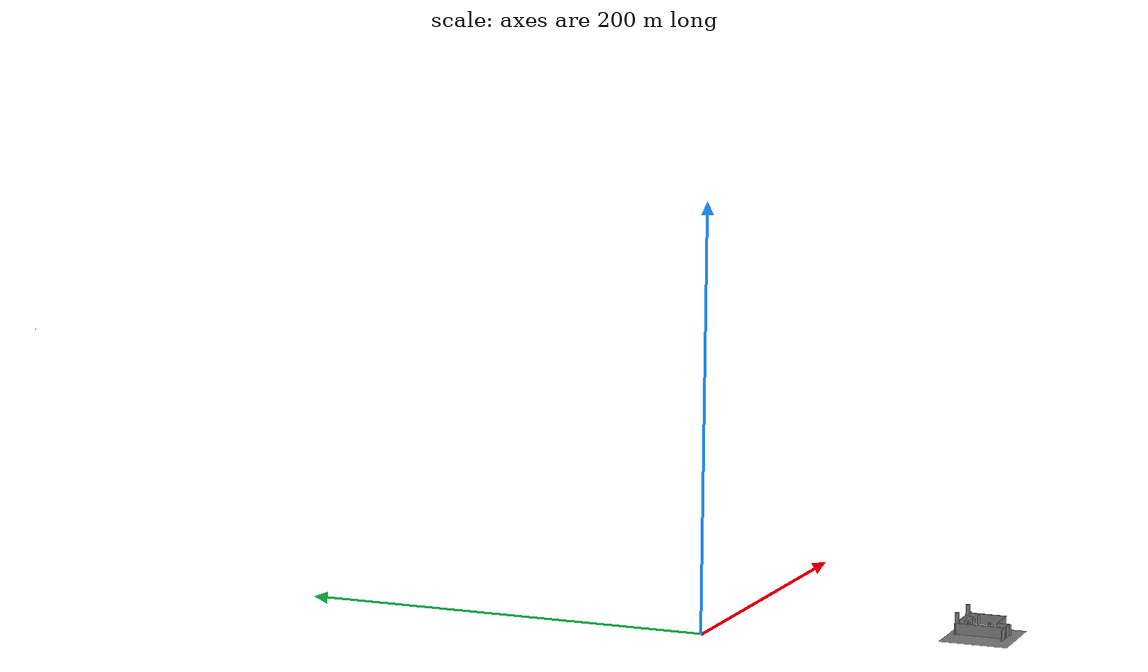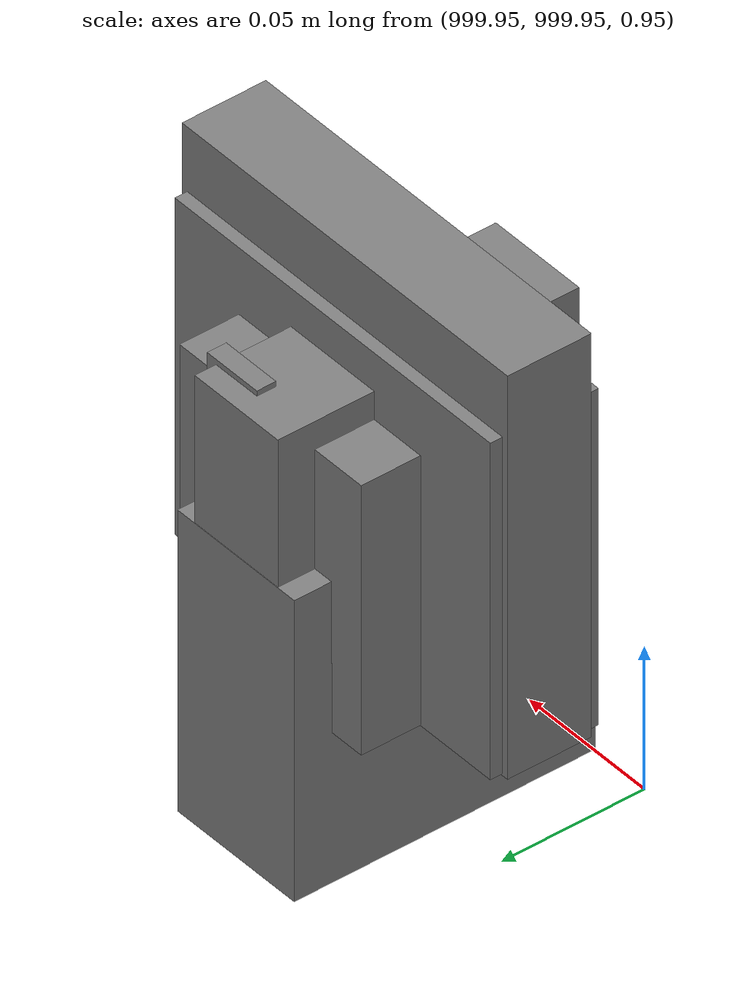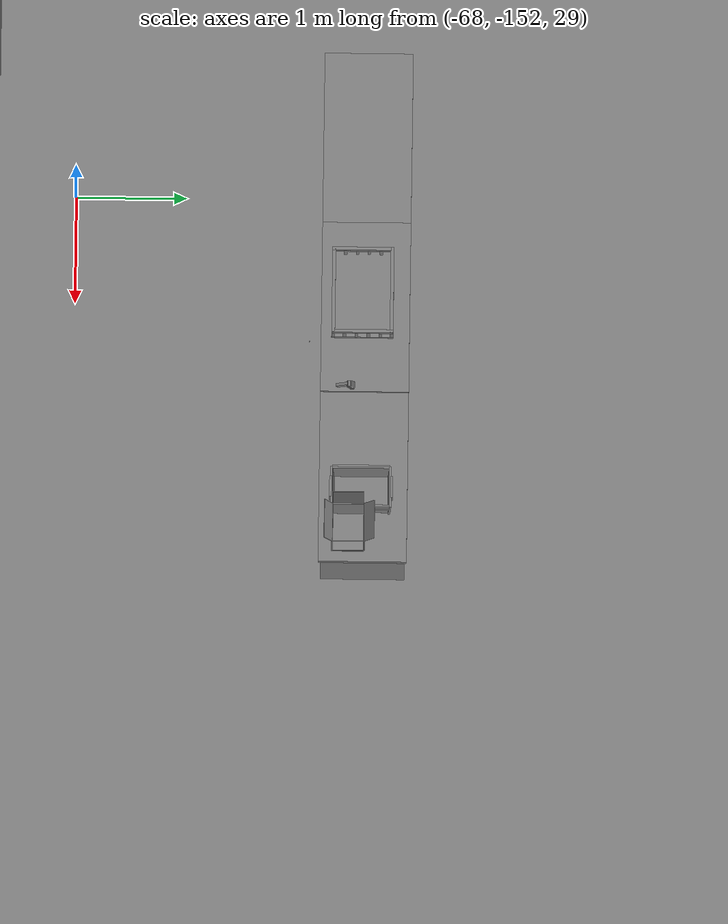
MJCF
<mujoco>
    <option gravity="0.000000000 0.000000000 -9.810000420" timestep="0.0049999999" integrator="implicitfast" density="1.225" viscosity="1.8000001e-05" noslip_iterations="10" iterations="100" sdf_iterations="50">
        <flag multiccd="disable"/>
    </option>
    <size memory="1000M"/>
    <compiler coordinate="local"/>
    <worldbody>
        <light cutoff="30" pos="0 1 1" dir="0 -1 -2"/>
        <light cutoff="30" pos="0 -1 1" dir="0 1 -2"/>
        <body pos="-64.866622925 -149.383972168 30.183746338" euler="89.999984741 89.999946594 0.000000000" name="openloong_gripper_2f85_fix_base_usda_bluebox_01">
            <geom contype="1" conaffinity="1" density="1000" type="box" material="" rgba="0.500000000 0.500000000 0.500000000 1.000000000" solimp="0.899999976 0.949999988 0.001000000" friction="1.000000000 0.005000000 0.000100000" solref="0.020000000 1.000000000" margin="0" condim="3" group="0" pos="0.276580811 0.187225342 0.000068665" quat="0.707106948 0.000077471 0.707106352 0.000077486" size="0.100000001 0.057999998 0.010000000" name="openloong_gripper_2f85_fix_base_usda_geom_FE33BADF_95F6_4DDB_AABF_896CA1E70A7B"/>
            <geom contype="1" conaffinity="1" density="1000" type="box" material="" rgba="0.500000000 0.500000000 0.500000000 1.000000000" solimp="0.899999976 0.949999988 0.001000000" friction="1.000000000 0.005000000 0.000100000" solref="0.020000000 1.000000000" margin="0" condim="3" group="0" pos="0.000000000 0.002883911 0.000000000" quat="0.999999881 0.000000000 0.000000000 0.000000000" size="0.254000008 0.003000000 0.172000006" name="openloong_gripper_2f85_fix_base_usda_geom_D102BCE6_4E30_4F2C_ABC1_A2A769411657"/>
            <geom contype="1" conaffinity="1" density="1000" type="box" material="" rgba="0.500000000 0.500000000 0.500000000 1.000000000" solimp="0.899999976 0.949999988 0.001000000" friction="1.000000000 0.005000000 0.000100000" solref="0.020000000 1.000000000" margin="0" condim="3" group="0" pos="0.000000000 0.124874115 0.173484802" quat="0.999796331 0.020176515 -0.000000015 0.000000030" size="0.259999990 0.119999997 0.007000000" name="openloong_gripper_2f85_fix_base_usda_geom_956C6558_767C_47DD_B8D3_B737ECD3BC41"/>
            <geom contype="1" conaffinity="1" density="1000" type="box" material="" rgba="0.500000000 0.500000000 0.500000000 1.000000000" solimp="0.899999976 0.949999988 0.001000000" friction="1.000000000 0.005000000 0.000100000" solref="0.020000000 1.000000000" margin="0" condim="3" group="0" pos="0.000000000 0.124874115 -0.173469543" quat="0.999796331 -0.020176545 -0.000000015 0.000000000" size="0.259999990 0.119999997 0.007000000" name="openloong_gripper_2f85_fix_base_usda_geom_B84E154D_E71D_4F80_9B53_45AFACBC791C"/>
            <geom contype="1" conaffinity="1" density="1000" type="box" material="" rgba="0.500000000 0.500000000 0.500000000 1.000000000" solimp="0.899999976 0.949999988 0.001000000" friction="1.000000000 0.005000000 0.000100000" solref="0.020000000 1.000000000" margin="0" condim="3" group="0" pos="0.000000000 0.214008331 0.188980103" quat="0.999912977 0.013176724 0.000000015 0.000000000" size="0.259999990 0.029999999 0.012500000" name="openloong_gripper_2f85_fix_base_usda_geom_A500A688_7B10_410D_BD9E_5E88900AEE3E"/>
            <geom contype="1" conaffinity="1" density="1000" type="box" material="" rgba="0.500000000 0.500000000 0.500000000 1.000000000" solimp="0.899999976 0.949999988 0.001000000" friction="1.000000000 0.005000000 0.000100000" solref="0.020000000 1.000000000" margin="0" condim="3" group="0" pos="-0.258361816 0.125289917 0.001876831" quat="0.702796936 -0.020792112 0.710783124 0.020769298" size="0.189999998 0.119999997 0.009000000" name="openloong_gripper_2f85_fix_base_usda_geom_CDA91506_8B15_4EE1_94FF_FCDA7DBB68FF"/>
            <geom contype="1" conaffinity="1" density="1000" type="box" material="" rgba="0.500000000 0.500000000 0.500000000 1.000000000" solimp="0.899999976 0.949999988 0.001000000" friction="1.000000000 0.005000000 0.000100000" solref="0.020000000 1.000000000" margin="0" condim="3" group="0" pos="0.000000000 0.214008331 -0.188980103" quat="0.999912977 -0.013176769 0.000000030 0.000000015" size="0.259999990 0.029999999 0.012500000" name="openloong_gripper_2f85_fix_base_usda_geom_B080A089_21D2_4242_82D4_3A47F9B8CA66"/>
            <geom contype="1" conaffinity="1" density="1000" type="box" material="" rgba="0.500000000 0.500000000 0.500000000 1.000000000" solimp="0.899999976 0.949999988 0.001000000" friction="1.000000000 0.005000000 0.000100000" solref="0.020000000 1.000000000" margin="0" condim="3" group="0" pos="-0.276611328 0.187225342 0.000068665" quat="0.707106650 0.000077441 0.707106709 0.000077456" size="0.100000001 0.057999998 0.010000000" name="openloong_gripper_2f85_fix_base_usda_geom_C30CB413_2D60_4E6F_89C4_338D643EEA7B"/>
            <geom contype="1" conaffinity="1" density="1000" type="box" material="" rgba="0.500000000 0.500000000 0.500000000 1.000000000" solimp="0.899999976 0.949999988 0.001000000" friction="1.000000000 0.005000000 0.000100000" solref="0.020000000 1.000000000" margin="0" condim="3" group="0" pos="0.258331299 0.125289917 0.001876831" quat="0.702851415 0.018856421 0.710823774 -0.019329369" size="0.189999998 0.119999997 0.009000000" name="openloong_gripper_2f85_fix_base_usda_geom_CF585F12_01B2_4723_945C_81FA43C29AD7"/>
            <freejoint name="openloong_gripper_2f85_fix_base_usda_bluebox_01_joint"/>
            <site size="0.005000000 0.005000000 0.005000000" rgba="0.500000000 0.500000000 0.500000000 1.000000000" pos="0.000000000 0.000000000 0.000000000" quat="0.999961913 0.008726534 0.000000000 0.000000000" group="0" type="sphere" name="openloong_gripper_2f85_fix_base_usda_bluebox_01site"/>
        </body>
        <body pos="-64.496299744 -149.491867065 30.235729218" euler="0.000000000 0.000000000 89.999946594" name="openloong_gripper_2f85_fix_base_usda_cardboardbox_01">
            <geom contype="1" conaffinity="1" density="1000" type="box" material="" rgba="0.500000000 0.500000000 0.500000000 1.000000000" solimp="0.899999976 0.949999988 0.001000000" friction="1.000000000 0.005000000 0.000100000" solref="0.020000000 1.000000000" margin="0" condim="3" group="0" pos="-0.003166199 -0.004086494 0.005052090" quat="1.000000000 0.000000000 0.000000000 0.000000000" size="0.142499998 0.177500010 0.005000000" name="openloong_gripper_2f85_fix_base_usda_geom_3880224D_856A_483E_9C95_07CFC6CB8947"/>
            <geom contype="1" conaffinity="1" density="1000" type="box" material="" rgba="0.500000000 0.500000000 0.500000000 1.000000000" solimp="0.899999976 0.949999988 0.001000000" friction="1.000000000 0.005000000 0.000100000" solref="0.020000000 1.000000000" margin="0" condim="3" group="0" pos="-0.003166199 0.170316696 0.150570869" quat="1.000000000 0.000000000 0.000000000 0.000000000" size="0.142499998 0.005000000 0.149999991" name="openloong_gripper_2f85_fix_base_usda_geom_717CCD76_54FD_4953_ACE1_796DC879E7E1"/>
            <geom contype="1" conaffinity="1" density="1000" type="box" material="" rgba="0.500000000 0.500000000 0.500000000 1.000000000" solimp="0.899999976 0.949999988 0.001000000" friction="1.000000000 0.005000000 0.000100000" solref="0.020000000 1.000000000" margin="0" condim="3" group="0" pos="-0.147399902 -0.005307198 0.150570869" quat="1.000000000 0.000000000 0.000000000 0.000000000" size="0.005000000 0.177500010 0.149999991" name="openloong_gripper_2f85_fix_base_usda_geom_1C730636_EC9F_41D6_8246_B6892A5EC499"/>
            <geom contype="1" conaffinity="1" density="1000" type="box" material="" rgba="0.500000000 0.500000000 0.500000000 1.000000000" solimp="0.899999976 0.949999988 0.001000000" friction="1.000000000 0.005000000 0.000100000" solref="0.020000000 1.000000000" margin="0" condim="3" group="0" pos="0.140275955 -0.005307198 0.150570869" quat="1.000000000 0.000000000 0.000000000 0.000000000" size="0.005000000 0.177500010 0.149999991" name="openloong_gripper_2f85_fix_base_usda_geom_31F899B7_6A2D_4B37_AFB0_85A3D269EBAD"/>
            <geom contype="1" conaffinity="1" density="1000" type="box" material="" rgba="0.500000000 0.500000000 0.500000000 1.000000000" solimp="0.899999976 0.949999988 0.001000000" friction="1.000000000 0.005000000 0.000100000" solref="0.020000000 1.000000000" margin="0" condim="3" group="0" pos="-0.003166199 -0.181550980 0.150570869" quat="1.000000000 0.000000000 0.000000000 0.000000000" size="0.142499998 0.005000000 0.149999991" name="openloong_gripper_2f85_fix_base_usda_geom_AD6BFBEA_AD97_4628_B0A4_903D04AF40C6"/>
            <freejoint name="openloong_gripper_2f85_fix_base_usda_cardboardbox_01_joint"/>
            <site size="0.005000000 0.005000000 0.005000000" rgba="0.500000000 0.500000000 0.500000000 1.000000000" pos="0.000000000 0.000000000 0.000000000" quat="0.999961913 0.008726535 0.000000000 0.000000000" group="0" type="sphere" name="openloong_gripper_2f85_fix_base_usda_site_36B1BD34_7C98_47B4_887A_7E708BDA18EA"/>
            <body pos="0.139160156 -0.004048347 0.301930904" euler="-179.999954224 49.383502960 179.999954224" name="openloong_gripper_2f85_fix_base_usda_A1_006">
                <geom contype="1" conaffinity="1" density="1000" type="box" material="" rgba="0.500000000 0.500000000 0.500000000 1.000000000" solimp="0.899999976 0.949999988 0.001000000" friction="1.000000000 0.005000000 0.000100000" solref="0.020000000 1.000000000" margin="0" condim="3" group="0" pos="-0.071587563 0.000009537 0.001745224" quat="0.999999881 0.000000000 0.000000000 0.000000000" size="0.071249999 0.179999992 0.002500000" name="openloong_gripper_2f85_fix_base_usda_geom_F9F4AF4A_3AD4_4D01_ACE8_CB0BCB2515F3"/>
                <joint armature="0" stiffness="0.07" damping="0.0099999998" axis="0.000000 1.000000 0.000000" type="hinge" name="openloong_gripper_2f85_fix_base_usda_A1_006"/>
            </body>
            <body pos="-0.145902634 -0.004086494 0.301938057" euler="-180.000000000 -60.000011444 -180.000000000" name="openloong_gripper_2f85_fix_base_usda_A2_006">
                <geom contype="1" conaffinity="1" density="1000" type="box" material="" rgba="0.500000000 0.500000000 0.500000000 1.000000000" solimp="0.899999976 0.949999988 0.001000000" friction="1.000000000 0.005000000 0.000100000" solref="0.020000000 1.000000000" margin="0" condim="3" group="0" pos="0.071268082 0.000009537 0.002717972" quat="0.000002921 0.000000000 -0.000000030 0.999999881" size="0.071249999 0.179999992 0.002500000" name="openloong_gripper_2f85_fix_base_usda_geom_BCE06ABA_A880_438A_A5A7_818E53B2E0B6"/>
                <joint armature="0" stiffness="0.07" damping="0.0099999998" axis="0.000000 1.000000 0.000000" type="hinge" name="openloong_gripper_2f85_fix_base_usda_A2_006"/>
            </body>
            <body pos="-0.003385544 0.175991058 0.301930904" euler="-125.858116150 -0.000004561 0.000002331" name="openloong_gripper_2f85_fix_base_usda_B2_006">
                <geom contype="1" conaffinity="1" density="1000" type="box" material="" rgba="0.500000000 0.500000000 0.500000000 1.000000000" solimp="0.899999976 0.949999988 0.001000000" friction="1.000000000 0.005000000 0.000100000" solref="0.020000000 1.000000000" margin="0" condim="3" group="0" pos="0.000009537 -0.070939064 -0.002470016" quat="0.999614120 0.027776197 -0.000000015 0.000000030" size="0.137500003 0.064999998 0.005000000" name="openloong_gripper_2f85_fix_base_usda_geom_0B65DE69_E797_41B0_B069_AF7F4E47C1AC"/>
                <joint armature="0" stiffness="0.07" damping="0.0099999998" axis="1.000000 0.000000 0.000000" type="hinge" name="openloong_gripper_2f85_fix_base_usda_B2_006"/>
            </body>
            <body pos="-0.003385544 -0.184140205 0.301938057" euler="147.805557251 0.000000000 0.000000000" name="openloong_gripper_2f85_fix_base_usda_B1_006">
                <geom contype="1" conaffinity="1" density="1000" type="box" material="" rgba="0.500000000 0.500000000 0.500000000 1.000000000" solimp="0.899999976 0.949999988 0.001000000" friction="1.000000000 0.005000000 0.000100000" solref="0.020000000 1.000000000" margin="0" condim="3" group="0" pos="-0.000028610 0.070202351 -0.002703667" quat="0.999614179 -0.027776167 0.000000000 0.000000000" size="0.137500003 0.064999998 0.005000000" name="openloong_gripper_2f85_fix_base_usda_geom_16D1AB01_7EA5_4D65_A9A5_6DD1C82CF1A6"/>
                <joint armature="0" stiffness="0.07" damping="0.0099999998" axis="1.000000 0.000000 0.000000" type="hinge" name="openloong_gripper_2f85_fix_base_usda_B1_006"/>
            </body>
        </body>
        <body pos="-65.882858276 -149.481979370 30.229999542" euler="-64.487716675 0.000000000 0.000000000" name="openloong_gripper_2f85_fix_base_usda_Barcode">
            <geom contype="1" conaffinity="1" density="1000" type="box" material="" rgba="0.500000000 0.500000000 0.500000000 1.000000000" solimp="0.899999976 0.949999988 0.001000000" friction="1.000000000 0.005000000 0.000100000" solref="0.020000000 1.000000000" margin="0" condim="3" group="0" pos="0.000000000 0.013038635 0.001419067" quat="0.000000000 0.000000000 0.000000000 1.000000119" size="0.034000002 0.010000000 0.017999999" name="openloong_gripper_2f85_fix_base_usda_geom_94B93569_8F9E_4941_A4DD_80CF47750ABE"/>
            <geom contype="1" conaffinity="1" density="1000" type="box" material="" rgba="0.500000000 0.500000000 0.500000000 1.000000000" solimp="0.899999976 0.949999988 0.001000000" friction="1.000000000 0.005000000 0.000100000" solref="0.020000000 1.000000000" margin="0" condim="3" group="0" pos="0.000000000 -0.035301208 -0.007095337" quat="0.000000000 0.000000000 -0.043619365 0.999048233" size="0.028999999 0.010000000 0.020000000" name="openloong_gripper_2f85_fix_base_usda_geom_CD501C8D_97CF_4CD2_99EE_C06E93DA2F3F"/>
            <geom contype="1" conaffinity="1" density="1000" type="box" material="" rgba="0.500000000 0.500000000 0.500000000 1.000000000" solimp="0.899999976 0.949999988 0.001000000" friction="1.000000000 0.005000000 0.000100000" solref="0.020000000 1.000000000" margin="0" condim="3" group="0" pos="0.000000000 -0.043411255 -0.011749268" quat="0.922262907 0.386563420 0.000000000 0.000000000" size="0.026000001 0.010000000 0.020000000" name="openloong_gripper_2f85_fix_base_usda_geom_1E78AFD3_83C1_4A71_B64C_1291323EE1DB"/>
            <geom contype="1" conaffinity="1" density="1000" type="box" material="" rgba="0.500000000 0.500000000 0.500000000 1.000000000" solimp="0.899999976 0.949999988 0.001000000" friction="1.000000000 0.005000000 0.000100000" solref="0.020000000 1.000000000" margin="0" condim="3" group="0" pos="0.000000000 -0.016967773 -0.031860352" quat="0.000000000 0.000000000 0.000000000 1.000000119" size="0.008000000 0.010000000 0.013000000" name="openloong_gripper_2f85_fix_base_usda_geom_7AE323D3_D951_464B_92FE_EC4FCEEC1E80"/>
            <geom contype="1" conaffinity="1" density="1000" type="box" material="" rgba="0.500000000 0.500000000 0.500000000 1.000000000" solimp="0.899999976 0.949999988 0.001000000" friction="1.000000000 0.005000000 0.000100000" solref="0.020000000 1.000000000" margin="0" condim="3" group="0" pos="0.000000000 -0.001869202 0.000312805" quat="0.953716993 0.300705761 0.000000000 0.000000000" size="0.032000002 0.010000000 0.018999999" name="openloong_gripper_2f85_fix_base_usda_geom_48ADAFB4_9A9A_40A2_87FF_BEEE55F6973C"/>
            <geom contype="1" conaffinity="1" density="1000" type="box" material="" rgba="0.500000000 0.500000000 0.500000000 1.000000000" solimp="0.899999976 0.949999988 0.001000000" friction="1.000000000 0.005000000 0.000100000" solref="0.020000000 1.000000000" margin="0" condim="3" group="0" pos="0.000000000 -0.019531250 -0.003173828" quat="0.953716993 0.300705761 0.000000000 0.000000000" size="0.030999999 0.010000000 0.020000000" name="openloong_gripper_2f85_fix_base_usda_geom_6FA52E32_225D_41F2_BCD2_D43DA8A3933D"/>
            <geom contype="1" conaffinity="1" density="1000" type="box" material="" rgba="0.500000000 0.500000000 0.500000000 1.000000000" solimp="0.899999976 0.949999988 0.001000000" friction="1.000000000 0.005000000 0.000100000" solref="0.020000000 1.000000000" margin="0" condim="3" group="0" pos="0.000000000 -0.035301208 -0.007095337" quat="0.953716993 0.300705761 0.000000000 0.000000000" size="0.028999999 0.010000000 0.020000000" name="openloong_gripper_2f85_fix_base_usda_geom_D9DE67A5_B81A_4E30_8D92_209B3485BFF4"/>
            <geom contype="1" conaffinity="1" density="1000" type="box" material="" rgba="0.500000000 0.500000000 0.500000000 1.000000000" solimp="0.899999976 0.949999988 0.001000000" friction="1.000000000 0.005000000 0.000100000" solref="0.020000000 1.000000000" margin="0" condim="3" group="0" pos="0.000000000 -0.042617798 -0.071121216" quat="0.000000000 0.000000000 0.000000000 1.000000119" size="0.013000000 0.021000000 0.059999999" name="openloong_gripper_2f85_fix_base_usda_geom_2A9803F1_2C08_435C_BAFD_902FCF8C81B9"/>
            <freejoint name="openloong_gripper_2f85_fix_base_usda_Barcode_joint"/>
            <site size="0.005000000 0.005000000 0.005000000" rgba="0.500000000 0.500000000 0.500000000 1.000000000" pos="0.000000000 0.000000000 0.000000000" quat="1.000000000 0.000000000 0.000000000 0.000000000" group="0" type="sphere" name="openloong_gripper_2f85_fix_base_usda_Barcode_site"/>
        </body>
        <body pos="-66.745018005 -149.392349243 30.184000015" euler="0.000000000 0.000000000 89.999946594" name="[22330687774624]_Basket_01">
            <geom contype="1" conaffinity="1" density="1000" type="box" material="" rgba="0.500000000 0.500000000 0.500000000 1.000000000" solimp="0.899999976 0.949999988 0.001000000" friction="1.000000000 0.005000000 0.000100000" solref="0.020000000 1.000000000" margin="0" condim="3" group="0" pos="-0.052425385 0.389207840 0.089787483" quat="0.707107008 0.000000000 0.000000000 0.707106411" size="0.014249999 0.014249999 0.059999999" name="[22330687774624]_geom_7CF752CF_0A5E_4555_9075_2434972F0392"/>
            <geom contype="1" conaffinity="1" density="1000" type="box" material="" rgba="0.500000000 0.500000000 0.500000000 1.000000000" solimp="0.899999976 0.949999988 0.001000000" friction="1.000000000 0.005000000 0.000100000" solref="0.020000000 1.000000000" margin="0" condim="3" group="0" pos="0.264015198 -0.133043289 0.089787483" quat="0.707107008 0.000000000 0.000000000 0.707106411" size="0.014249999 0.014249999 0.059999999" name="[22330687774624]_geom_05C13118_0D08_4319_AB75_97BC15C664BE"/>
            <geom contype="1" conaffinity="1" density="1000" type="box" material="" rgba="0.500000000 0.500000000 0.500000000 1.000000000" solimp="0.899999976 0.949999988 0.001000000" friction="1.000000000 0.005000000 0.000100000" solref="0.020000000 1.000000000" margin="0" condim="3" group="0" pos="-0.264015198 -0.265548706 0.089793205" quat="0.707107008 0.000000000 0.000000000 0.707106411" size="0.014249999 0.014249999 0.059999999" name="[22330687774624]_geom_97702646_D1C5_4924_862A_625F6D3CDE04"/>
            <geom contype="1" conaffinity="1" density="1000" type="box" material="" rgba="0.500000000 0.500000000 0.500000000 1.000000000" solimp="0.899999976 0.949999988 0.001000000" friction="1.000000000 0.005000000 0.000100000" solref="0.020000000 1.000000000" margin="0" condim="3" group="0" pos="-0.160263062 -0.389322281 0.089793205" quat="0.707107008 0.000000000 0.000000000 0.707106411" size="0.014249999 0.014249999 0.059999999" name="[22330687774624]_geom_27C609F5_6FF8_4DB7_B063_F36116F9CBB8"/>
            <geom contype="1" conaffinity="1" density="1000" type="box" material="" rgba="0.500000000 0.500000000 0.500000000 1.000000000" solimp="0.899999976 0.949999988 0.001000000" friction="1.000000000 0.005000000 0.000100000" solref="0.020000000 1.000000000" margin="0" condim="3" group="0" pos="0.162265778 -0.389322281 0.089787483" quat="0.707107008 0.000000000 0.000000000 0.707106411" size="0.014249999 0.014249999 0.059999999" name="[22330687774624]_geom_42EB2995_81D2_40D6_8B05_57524817BD37"/>
            <geom contype="1" conaffinity="1" density="1000" type="box" material="" rgba="0.500000000 0.500000000 0.500000000 1.000000000" solimp="0.899999976 0.949999988 0.001000000" friction="1.000000000 0.005000000 0.000100000" solref="0.020000000 1.000000000" margin="0" condim="3" group="0" pos="0.264015198 0.389207840 0.089787483" quat="0.707107008 0.000000000 0.000000000 0.707106411" size="0.014249999 0.014249999 0.059999999" name="[22330687774624]_geom_D8F67B7A_C8EA_401E_A881_E86FF48A4C1E"/>
            <geom contype="1" conaffinity="1" density="1000" type="box" material="" rgba="0.500000000 0.500000000 0.500000000 1.000000000" solimp="0.899999976 0.949999988 0.001000000" friction="1.000000000 0.005000000 0.000100000" solref="0.020000000 1.000000000" margin="0" condim="3" group="0" pos="-0.264015198 -0.133043289 0.089793205" quat="0.707107008 0.000000000 0.000000000 0.707106411" size="0.014249999 0.014249999 0.059999999" name="[22330687774624]_geom_EF3064D5_8F18_42A5_B9CA_09940B7E8B68"/>
            <geom contype="1" conaffinity="1" density="1000" type="box" material="" rgba="0.500000000 0.500000000 0.500000000 1.000000000" solimp="0.899999976 0.949999988 0.001000000" friction="1.000000000 0.005000000 0.000100000" solref="0.020000000 1.000000000" margin="0" condim="3" group="0" pos="-0.264026642 0.269256592 0.089793205" quat="0.707107008 0.000000000 0.000000000 0.707106411" size="0.014249999 0.014249999 0.059999999" name="[22330687774624]_geom_3E866B6B_70BB_41A6_A6F2_4D8AB6B1AB17"/>
            <geom contype="1" conaffinity="1" density="1000" type="box" material="" rgba="0.500000000 0.500000000 0.500000000 1.000000000" solimp="0.899999976 0.949999988 0.001000000" friction="1.000000000 0.005000000 0.000100000" solref="0.020000000 1.000000000" margin="0" condim="3" group="0" pos="0.054462433 0.389207840 0.089787483" quat="0.707107008 0.000000000 0.000000000 0.707106411" size="0.014249999 0.014249999 0.059999999" name="[22330687774624]_geom_60F44C80_0693_4377_8DB4_0B5E0BF429E3"/>
            <geom contype="1" conaffinity="1" density="1000" type="box" material="" rgba="0.500000000 0.500000000 0.500000000 1.000000000" solimp="0.899999976 0.949999988 0.001000000" friction="1.000000000 0.005000000 0.000100000" solref="0.020000000 1.000000000" margin="0" condim="3" group="0" pos="0.054462433 -0.389322281 0.089787483" quat="0.707107008 0.000000000 0.000000000 0.707106411" size="0.014249999 0.014249999 0.059999999" name="[22330687774624]_geom_B162BADF_6B97_478B_8222_3BFDCA2CDDDF"/>
            <geom contype="1" conaffinity="1" density="1000" type="box" material="" rgba="0.500000000 0.500000000 0.500000000 1.000000000" solimp="0.899999976 0.949999988 0.001000000" friction="1.000000000 0.005000000 0.000100000" solref="0.020000000 1.000000000" margin="0" condim="3" group="0" pos="0.264015198 0.269256592 0.089793205" quat="0.707107008 0.000000000 0.000000000 0.707106411" size="0.014249999 0.014249999 0.059999999" name="[22330687774624]_geom_2F531CC2_FCB3_4382_8327_7D7E9D7E4863"/>
            <geom contype="1" conaffinity="1" density="1000" type="box" material="" rgba="0.500000000 0.500000000 0.500000000 1.000000000" solimp="0.899999976 0.949999988 0.001000000" friction="1.000000000 0.005000000 0.000100000" solref="0.020000000 1.000000000" margin="0" condim="3" group="0" pos="0.264015198 -0.389322281 0.089787483" quat="0.707107008 0.000000000 0.000000000 0.707106411" size="0.014249999 0.014249999 0.059999999" name="[22330687774624]_geom_AC065EB0_98E2_48E7_A228_A5C90CA52F5D"/>
            <geom contype="1" conaffinity="1" density="1000" type="box" material="" rgba="0.500000000 0.500000000 0.500000000 1.000000000" solimp="0.899999976 0.949999988 0.001000000" friction="1.000000000 0.005000000 0.000100000" solref="0.020000000 1.000000000" margin="0" condim="3" group="0" pos="0.000000000 0.000000000 0.015998840" quat="0.707107008 0.000000000 0.000000000 0.707106411" size="0.403499991 0.279000014 0.015750000" name="[22330687774624]_geom_A8FA6638_4456_4DDF_B679_CB1D125CD199"/>
            <geom contype="1" conaffinity="1" density="1000" type="box" material="" rgba="0.500000000 0.500000000 0.500000000 1.000000000" solimp="0.899999976 0.949999988 0.001000000" friction="1.000000000 0.005000000 0.000100000" solref="0.020000000 1.000000000" margin="0" condim="3" group="0" pos="0.000000000 -0.389476776 0.163619041" quat="0.707107008 0.000000000 0.000000000 0.707106411" size="0.015000000 0.277500004 0.015750000" name="[22330687774624]_geom_88784CFF_280A_4784_B463_5EAE8870FDB3"/>
            <geom contype="1" conaffinity="1" density="1000" type="box" material="" rgba="0.500000000 0.500000000 0.500000000 1.000000000" solimp="0.899999976 0.949999988 0.001000000" friction="1.000000000 0.005000000 0.000100000" solref="0.020000000 1.000000000" margin="0" condim="3" group="0" pos="0.162265778 0.389207840 0.089787483" quat="0.707107008 0.000000000 0.000000000 0.707106411" size="0.014249999 0.014249999 0.059999999" name="[22330687774624]_geom_E0B2AEF7_EC8B_469B_BE94_7670FFDF8A15"/>
            <geom contype="1" conaffinity="1" density="1000" type="box" material="" rgba="0.500000000 0.500000000 0.500000000 1.000000000" solimp="0.899999976 0.949999988 0.001000000" friction="1.000000000 0.005000000 0.000100000" solref="0.020000000 1.000000000" margin="0" condim="3" group="0" pos="0.000000000 0.389471054 0.163619041" quat="0.707107008 0.000000000 0.000000000 0.707106411" size="0.015000000 0.277500004 0.015750000" name="[22330687774624]_geom_D00C7389_3BBD_43EA_A215_40957426710B"/>
            <geom contype="1" conaffinity="1" density="1000" type="box" material="" rgba="0.500000000 0.500000000 0.500000000 1.000000000" solimp="0.899999976 0.949999988 0.001000000" friction="1.000000000 0.005000000 0.000100000" solref="0.020000000 1.000000000" margin="0" condim="3" group="0" pos="-0.263511658 0.000000000 0.163619041" quat="0.707107008 0.000000000 0.000000000 0.707106411" size="0.403499991 0.015000000 0.015750000" name="[22330687774624]_geom_3800E59C_A6C5_4DA5_8CCB_5638E7AEB34D"/>
            <geom contype="1" conaffinity="1" density="1000" type="box" material="" rgba="0.500000000 0.500000000 0.500000000 1.000000000" solimp="0.899999976 0.949999988 0.001000000" friction="1.000000000 0.005000000 0.000100000" solref="0.020000000 1.000000000" margin="0" condim="3" group="0" pos="-0.264015198 0.141334534 0.089793205" quat="0.707107008 0.000000000 0.000000000 0.707106411" size="0.014249999 0.014249999 0.059999999" name="[22330687774624]_geom_F2939CC0_F6E6_4294_9B59_1429197D4FE1"/>
            <geom contype="1" conaffinity="1" density="1000" type="box" material="" rgba="0.500000000 0.500000000 0.500000000 1.000000000" solimp="0.899999976 0.949999988 0.001000000" friction="1.000000000 0.005000000 0.000100000" solref="0.020000000 1.000000000" margin="0" condim="3" group="0" pos="0.264015198 -0.265548706 0.089787483" quat="0.707107008 0.000000000 0.000000000 0.707106411" size="0.014249999 0.014249999 0.059999999" name="[22330687774624]_geom_0694A111_0305_4299_B552_364D27B7FC49"/>
            <geom contype="1" conaffinity="1" density="1000" type="box" material="" rgba="0.500000000 0.500000000 0.500000000 1.000000000" solimp="0.899999976 0.949999988 0.001000000" friction="1.000000000 0.005000000 0.000100000" solref="0.020000000 1.000000000" margin="0" condim="3" group="0" pos="-0.160263062 0.389207840 0.089787483" quat="0.707107008 0.000000000 0.000000000 0.707106411" size="0.014249999 0.014249999 0.059999999" name="[22330687774624]_geom_D0050EC8_3BAF_46DB_A152_C386E22461D3"/>
            <geom contype="1" conaffinity="1" density="1000" type="box" material="" rgba="0.500000000 0.500000000 0.500000000 1.000000000" solimp="0.899999976 0.949999988 0.001000000" friction="1.000000000 0.005000000 0.000100000" solref="0.020000000 1.000000000" margin="0" condim="3" group="0" pos="-0.052425385 -0.389322281 0.089787483" quat="0.707107008 0.000000000 0.000000000 0.707106411" size="0.014249999 0.014249999 0.059999999" name="[22330687774624]_geom_7D8C46B3_19CC_448F_8C28_593F6177F41F"/>
            <geom contype="1" conaffinity="1" density="1000" type="box" material="" rgba="0.500000000 0.500000000 0.500000000 1.000000000" solimp="0.899999976 0.949999988 0.001000000" friction="1.000000000 0.005000000 0.000100000" solref="0.020000000 1.000000000" margin="0" condim="3" group="0" pos="-0.264026642 -0.389322281 0.089793205" quat="0.707107008 0.000000000 0.000000000 0.707106411" size="0.014249999 0.014249999 0.059999999" name="[22330687774624]_geom_2E319722_0FEB_4508_A746_B4B7EB9C52F5"/>
            <geom contype="1" conaffinity="1" density="1000" type="box" material="" rgba="0.500000000 0.500000000 0.500000000 1.000000000" solimp="0.899999976 0.949999988 0.001000000" friction="1.000000000 0.005000000 0.000100000" solref="0.020000000 1.000000000" margin="0" condim="3" group="0" pos="0.264015198 0.141334534 0.089787483" quat="0.707107008 0.000000000 0.000000000 0.707106411" size="0.014249999 0.014249999 0.059999999" name="[22330687774624]_geom_5AE4A552_F5CE_4126_8103_A6EE2A536755"/>
            <geom contype="1" conaffinity="1" density="1000" type="box" material="" rgba="0.500000000 0.500000000 0.500000000 1.000000000" solimp="0.899999976 0.949999988 0.001000000" friction="1.000000000 0.005000000 0.000100000" solref="0.020000000 1.000000000" margin="0" condim="3" group="0" pos="-0.264015198 0.389207840 0.089793205" quat="0.707107008 0.000000000 0.000000000 0.707106411" size="0.014249999 0.014249999 0.059999999" name="[22330687774624]_geom_5AB9DAC2_C2BB_4C73_B19D_CD8F8F3D5058"/>
            <geom contype="1" conaffinity="1" density="1000" type="box" material="" rgba="0.500000000 0.500000000 0.500000000 1.000000000" solimp="0.899999976 0.949999988 0.001000000" friction="1.000000000 0.005000000 0.000100000" solref="0.020000000 1.000000000" margin="0" condim="3" group="0" pos="0.264015198 0.004480362 0.089787483" quat="0.707107008 0.000000000 0.000000000 0.707106411" size="0.014249999 0.014249999 0.059999999" name="[22330687774624]_geom_586945C1_5EC6_42F3_A436_081959A8C5D6"/>
            <geom contype="1" conaffinity="1" density="1000" type="box" material="" rgba="0.500000000 0.500000000 0.500000000 1.000000000" solimp="0.899999976 0.949999988 0.001000000" friction="1.000000000 0.005000000 0.000100000" solref="0.020000000 1.000000000" margin="0" condim="3" group="0" pos="0.263694763 -0.000011444 0.163619041" quat="0.707107008 0.000000000 0.000000000 0.707106411" size="0.403499991 0.015000000 0.015750000" name="[22330687774624]_geom_728CC4BF_4EDE_4415_A1E0_49A430EDF904"/>
            <geom contype="1" conaffinity="1" density="1000" type="box" material="" rgba="0.500000000 0.500000000 0.500000000 1.000000000" solimp="0.899999976 0.949999988 0.001000000" friction="1.000000000 0.005000000 0.000100000" solref="0.020000000 1.000000000" margin="0" condim="3" group="0" pos="-0.264015198 0.004480362 0.089793205" quat="0.707107008 0.000000000 0.000000000 0.707106411" size="0.014249999 0.014249999 0.059999999" name="[22330687774624]_geom_B3B5C406_FE70_41B6_B75A_7BEFB9606938"/>
            <freejoint name="[22330687774624]_joint_516E9069_E9F8_4628_A3D7_73E31992EE60"/>
        </body>
        <body pos="0.000000000 0.000000000 0.000000000" euler="0.000000000 0.000000000 0.000000000" name="Static Objects_Static Objects">
            <geom contype="1" conaffinity="1" density="1000" type="box" material="" rgba="0.500000000 0.500000000 0.500000000 1.000000000" solimp="0.899999976 0.949999988 0.001000000" friction="1.000000000 0.005000000 0.000100000" solref="0.020000000 1.000000000" margin="0" condim="3" group="0" pos="-67.544113159 -149.365814209 29.727830887" quat="0.500000417 0.499999970 0.499999553 0.499999970" size="0.381000012 0.319999993 0.041000001" name="Static Objects_geom_8468279E_7AFF_4B73_AE4D_6667E13E3E70"/>
            <geom contype="1" conaffinity="1" density="1000" type="box" material="" rgba="0.500000000 0.500000000 0.500000000 1.000000000" solimp="0.899999976 0.949999988 0.001000000" friction="1.000000000 0.005000000 0.000100000" solref="0.020000000 1.000000000" margin="0" condim="3" group="0" pos="-68.239501953 -149.365814209 30.086868286" quat="0.500000417 0.499999970 0.499999553 0.499999970" size="0.370999992 0.039500002 0.745000005" name="Static Objects_geom_A9516C32_D667_47FB_A259_73FFB2F42808"/>
            <geom contype="1" conaffinity="1" density="1000" type="box" material="" rgba="0.500000000 0.500000000 0.500000000 1.000000000" solimp="0.899999976 0.949999988 0.001000000" friction="1.000000000 0.005000000 0.000100000" solref="0.020000000 1.000000000" margin="0" condim="3" group="0" pos="-68.239501953 -149.365814209 30.147235870" quat="0.500000417 0.499999970 0.499999553 0.499999970" size="0.400000006 0.022000000 0.800000012" name="Static Objects_geom_BDA3BB5D_3EB5_42C3_A983_FD2296B1D17E"/>
            <geom contype="1" conaffinity="1" density="1000" type="box" material="" rgba="0.500000000 0.500000000 0.500000000 1.000000000" solimp="0.899999976 0.949999988 0.001000000" friction="1.000000000 0.005000000 0.000100000" solref="0.020000000 1.000000000" margin="0" condim="3" group="0" pos="-68.934890747 -149.365814209 29.727830887" quat="0.500000417 0.499999970 0.499999553 0.499999970" size="0.381000012 0.319999993 0.041000001" name="Static Objects_geom_56E6F416_7B0C_49A0_BAD9_110ABD87129A"/>
            <geom contype="1" conaffinity="1" density="1000" type="box" material="" rgba="0.500000000 0.500000000 0.500000000 1.000000000" solimp="0.899999976 0.949999988 0.001000000" friction="1.000000000 0.005000000 0.000100000" solref="0.020000000 1.000000000" margin="0" condim="3" group="0" pos="-68.239501953 -149.365814209 29.561563492" quat="0.500000417 0.499999970 0.499999553 0.499999970" size="0.020000000 0.022000000 0.660000026" name="Static Objects_geom_4826637E_6F77_40BB_BA84_D906D5D22242"/>
            <geom contype="1" conaffinity="1" density="1000" type="box" material="" rgba="0.500000000 0.500000000 0.500000000 1.000000000" solimp="0.899999976 0.949999988 0.001000000" friction="1.000000000 0.005000000 0.000100000" solref="0.020000000 1.000000000" margin="0" condim="3" group="0" pos="-65.945671082 -149.365814209 29.727830887" quat="0.500000417 0.499999970 0.499999553 0.499999970" size="0.381000012 0.319999993 0.041000001" name="Static Objects_geom_C040880A_D94D_42F9_9594_6B49C679A3E4"/>
            <geom contype="1" conaffinity="1" density="1000" type="box" material="" rgba="0.500000000 0.500000000 0.500000000 1.000000000" solimp="0.899999976 0.949999988 0.001000000" friction="1.000000000 0.005000000 0.000100000" solref="0.020000000 1.000000000" margin="0" condim="3" group="0" pos="-66.641059875 -149.365814209 30.086868286" quat="0.500000417 0.499999970 0.499999553 0.499999970" size="0.370999992 0.039500002 0.745000005" name="Static Objects_geom_E31F1901_968A_4C9B_9358_1A523835C51B"/>
            <geom contype="1" conaffinity="1" density="1000" type="box" material="" rgba="0.500000000 0.500000000 0.500000000 1.000000000" solimp="0.899999976 0.949999988 0.001000000" friction="1.000000000 0.005000000 0.000100000" solref="0.020000000 1.000000000" margin="0" condim="3" group="0" pos="-66.641059875 -149.365814209 30.147235870" quat="0.500000417 0.499999970 0.499999553 0.499999970" size="0.400000006 0.022000000 0.800000012" name="Static Objects_geom_E7F982F5_52C7_4C4A_84F0_4823CF27899E"/>
            <geom contype="1" conaffinity="1" density="1000" type="box" material="" rgba="0.500000000 0.500000000 0.500000000 1.000000000" solimp="0.899999976 0.949999988 0.001000000" friction="1.000000000 0.005000000 0.000100000" solref="0.020000000 1.000000000" margin="0" condim="3" group="0" pos="-67.336448669 -149.365814209 29.727830887" quat="0.500000417 0.499999970 0.499999553 0.499999970" size="0.381000012 0.319999993 0.041000001" name="Static Objects_geom_05996935_D009_469E_A223_9615ECF3CAAE"/>
            <geom contype="1" conaffinity="1" density="1000" type="box" material="" rgba="0.500000000 0.500000000 0.500000000 1.000000000" solimp="0.899999976 0.949999988 0.001000000" friction="1.000000000 0.005000000 0.000100000" solref="0.020000000 1.000000000" margin="0" condim="3" group="0" pos="-66.641059875 -149.365814209 29.561563492" quat="0.500000417 0.499999970 0.499999553 0.499999970" size="0.020000000 0.022000000 0.660000026" name="Static Objects_geom_53E90519_6BDA_45E1_9E66_DFEE2EE1A791"/>
            <geom contype="1" conaffinity="1" density="1000" type="box" material="" rgba="0.500000000 0.500000000 0.500000000 1.000000000" solimp="0.899999976 0.949999988 0.001000000" friction="1.000000000 0.005000000 0.000100000" solref="0.020000000 1.000000000" margin="0" condim="3" group="0" pos="-64.338577271 -149.365814209 29.727830887" quat="0.500000417 0.499999970 0.499999553 0.499999970" size="0.381000012 0.319999993 0.041000001" name="Static Objects_geom_A591C3F7_02FA_41FC_B562_092E945AF04F"/>
            <geom contype="1" conaffinity="1" density="1000" type="box" material="" rgba="0.500000000 0.500000000 0.500000000 1.000000000" solimp="0.899999976 0.949999988 0.001000000" friction="1.000000000 0.005000000 0.000100000" solref="0.020000000 1.000000000" margin="0" condim="3" group="0" pos="-65.033966064 -149.365814209 30.086868286" quat="0.500000417 0.499999970 0.499999553 0.499999970" size="0.370999992 0.039500002 0.745000005" name="Static Objects_geom_85D44C12_E2E3_4988_AABE_9B907F978213"/>
            <geom contype="1" conaffinity="1" density="1000" type="box" material="" rgba="0.500000000 0.500000000 0.500000000 1.000000000" solimp="0.899999976 0.949999988 0.001000000" friction="1.000000000 0.005000000 0.000100000" solref="0.020000000 1.000000000" margin="0" condim="3" group="0" pos="-65.033966064 -149.365814209 30.147235870" quat="0.500000417 0.499999970 0.499999553 0.499999970" size="0.400000006 0.022000000 0.800000012" name="Static Objects_geom_6F48781E_5D25_430D_A143_42650C564437"/>
            <geom contype="1" conaffinity="1" density="1000" type="box" material="" rgba="0.500000000 0.500000000 0.500000000 1.000000000" solimp="0.899999976 0.949999988 0.001000000" friction="1.000000000 0.005000000 0.000100000" solref="0.020000000 1.000000000" margin="0" condim="3" group="0" pos="-65.729354858 -149.365814209 29.727830887" quat="0.500000417 0.499999970 0.499999553 0.499999970" size="0.381000012 0.319999993 0.041000001" name="Static Objects_geom_CF9769D4_1698_4782_9C19_A95594345742"/>
            <geom contype="1" conaffinity="1" density="1000" type="box" material="" rgba="0.500000000 0.500000000 0.500000000 1.000000000" solimp="0.899999976 0.949999988 0.001000000" friction="1.000000000 0.005000000 0.000100000" solref="0.020000000 1.000000000" margin="0" condim="3" group="0" pos="-65.033966064 -149.365814209 29.561563492" quat="0.500000417 0.499999970 0.499999553 0.499999970" size="0.020000000 0.022000000 0.660000026" name="Static Objects_geom_225E0543_B2C7_4D50_929F_D41E43720CE8"/>
            <geom contype="1" conaffinity="1" density="1000" type="box" material="" rgba="0.500000000 0.500000000 0.500000000 1.000000000" solimp="0.899999976 0.949999988 0.001000000" friction="1.000000000 0.005000000 0.000100000" solref="0.020000000 1.000000000" margin="0" condim="3" group="0" pos="-61.754566193 -137.853729248 33.906845093" quat="0.707107067 0.000000000 0.000000000 0.707106471" size="0.759999990 0.759999990 4.500000000" name="Static Objects_geom_4F4B14F7_38ED_459C_977E_48A720121867"/>
            <geom contype="1" conaffinity="1" density="1000" type="box" material="" rgba="0.500000000 0.500000000 0.500000000 1.000000000" solimp="0.899999976 0.949999988 0.001000000" friction="1.000000000 0.005000000 0.000100000" solref="0.020000000 1.000000000" margin="0" condim="3" group="0" pos="-57.511135101 -144.927108765 31.707921982" quat="1.000000000 0.000000000 0.000000000 0.000000000" size="0.200000003 8.000000000 2.299999952" name="Static Objects_geom_464884F1_A348_4EF9_A600_D2DFEB3950CE"/>
            <geom contype="1" conaffinity="1" density="1000" type="box" material="" rgba="0.500000000 0.500000000 0.500000000 1.000000000" solimp="0.899999976 0.949999988 0.001000000" friction="1.000000000 0.005000000 0.000100000" solref="0.020000000 1.000000000" margin="0" condim="3" group="0" pos="-80.517646790 -157.574050903 31.688196182" quat="0.707107067 0.000000000 0.000000000 0.707106471" size="0.600000024 0.600000024 2.299999952" name="Static Objects_geom_7F3BF8C1_0FFB_4BCF_8F68_81C4AE2E322D"/>
            <geom contype="1" conaffinity="1" density="1000" type="box" material="" rgba="0.500000000 0.500000000 0.500000000 1.000000000" solimp="0.899999976 0.949999988 0.001000000" friction="1.000000000 0.005000000 0.000100000" solref="0.020000000 1.000000000" margin="0" condim="3" group="0" pos="-80.711044312 -147.414932251 31.666158676" quat="1.000000000 0.000000000 0.000000000 0.000000000" size="0.200000003 10.000000000 2.299999952" name="Static Objects_geom_64096141_2144_4E3E_A0B1_C67ABC69F1D1"/>
            <geom contype="1" conaffinity="1" density="1000" type="box" material="" rgba="0.500000000 0.500000000 0.500000000 1.000000000" solimp="0.899999976 0.949999988 0.001000000" friction="1.000000000 0.005000000 0.000100000" solref="0.020000000 1.000000000" margin="0" condim="3" group="0" pos="-57.687217712 -137.434692383 31.688196182" quat="0.707107067 0.000000000 0.000000000 0.707106471" size="0.600000024 0.600000024 2.299999952" name="Static Objects_geom_4FD5A871_452D_4FE2_857C_D3FFDB65DA93"/>
            <geom contype="1" conaffinity="1" density="1000" type="box" material="" rgba="0.500000000 0.500000000 0.500000000 1.000000000" solimp="0.899999976 0.949999988 0.001000000" friction="1.000000000 0.005000000 0.000100000" solref="0.020000000 1.000000000" margin="0" condim="3" group="0" pos="-69.537033081 -140.263229370 31.714921951" quat="0.707107067 0.000000000 0.000000000 0.707106471" size="0.759999990 4.500000000 2.299999952" name="Static Objects_geom_234B15C5_000D_4F95_9AC2_0AAA0E53BFDE"/>
            <geom contype="1" conaffinity="1" density="1000" type="box" material="" rgba="0.500000000 0.500000000 0.500000000 1.000000000" solimp="0.899999976 0.949999988 0.001000000" friction="1.000000000 0.005000000 0.000100000" solref="0.020000000 1.000000000" margin="0" condim="3" group="0" pos="-80.073638916 -137.853713989 33.906845093" quat="0.707107067 0.000000000 0.000000000 0.707106471" size="0.759999990 0.759999990 4.500000000" name="Static Objects_geom_60BA7013_695B_4BCE_AF11_8C9AEF4FF3E7"/>
            <geom contype="1" conaffinity="1" density="1000" type="box" material="" rgba="0.500000000 0.500000000 0.500000000 1.000000000" solimp="0.899999976 0.949999988 0.001000000" friction="1.000000000 0.005000000 0.000100000" solref="0.020000000 1.000000000" margin="0" condim="3" group="0" pos="-73.406707764 -155.734664917 31.707921982" quat="1.000000000 0.000000000 0.000000000 0.000000000" size="0.200000003 3.000000000 2.299999952" name="Static Objects_geom_C72C2C36_300E_45B6_9578_87A6FADBB60C"/>
            <geom contype="1" conaffinity="1" density="1000" type="box" material="" rgba="0.500000000 0.500000000 0.500000000 1.000000000" solimp="0.899999976 0.949999988 0.001000000" friction="1.000000000 0.005000000 0.000100000" solref="0.020000000 1.000000000" margin="0" condim="3" group="0" pos="-68.497543335 -137.448257446 31.707921982" quat="0.707107067 0.000000000 0.000000000 0.707106471" size="0.200000003 14.000000000 2.299999952" name="Static Objects_geom_728EDCDE_61C9_48C7_95CA_A6B60A1FE994"/>
            <geom contype="1" conaffinity="1" density="1000" type="cylinder" material="" rgba="0.500000000 0.500000000 0.500000000 1.000000000" solimp="0.899999976 0.949999988 0.001000000" friction="1.000000000 0.005000000 0.000100000" solref="0.020000000 1.000000000" margin="0" condim="3" group="0" pos="-68.868522644 -142.134506226 31.711090088" quat="0.707107067 0.000000000 0.000000000 0.707106471" size="0.509999990 2.299999952 1.000000000" name="Static Objects_geom_F990E94D_48D6_4D88_A395_9A9BACD46344"/>
            <geom contype="1" conaffinity="1" density="1000" type="plane" material="" rgba="0.500000000 0.500000000 0.500000000 1.000000000" solimp="0.899999976 0.949999988 0.001000000" friction="1.000000000 0.005000000 0.000100000" solref="0.020000000 1.000000000" margin="0" condim="3" group="0" pos="-72.873703003 -147.131927490 29.409669876" quat="1.000000000 0.000000000 0.000000000 0.000000000" size="18.000000000 14.000000000 1.000000000" name="Static Objects_geom_5AF900A1_9C6C_4F7C_84AA_680B3D700630"/>
            <geom contype="1" conaffinity="1" density="1000" type="box" material="" rgba="0.500000000 0.500000000 0.500000000 1.000000000" solimp="0.899999976 0.949999988 0.001000000" friction="1.000000000 0.005000000 0.000100000" solref="0.020000000 1.000000000" margin="0" condim="3" group="0" pos="-79.943580627 -157.782272339 31.707921982" quat="0.707107067 0.000000000 0.000000000 0.707106471" size="0.200000003 7.000000000 2.299999952" name="Static Objects_geom_833C4236_2D9A_462B_B041_F1BF22B663C8"/>
            <geom contype="1" conaffinity="1" density="1000" type="box" material="" rgba="0.500000000 0.500000000 0.500000000 1.000000000" solimp="0.899999976 0.949999988 0.001000000" friction="1.000000000 0.005000000 0.000100000" solref="0.020000000 1.000000000" margin="0" condim="3" group="0" pos="-65.421028137 -152.903442383 31.707921982" quat="0.707107067 0.000000000 0.000000000 0.707106471" size="0.200000003 7.800000191 2.299999952" name="Static Objects_geom_A178E6A6_CF7A_4C5F_A00F_BAF1010943AB"/>
            <geom contype="1" conaffinity="1" density="1000" type="box" material="" rgba="0.500000000 0.500000000 0.500000000 1.000000000" solimp="0.899999976 0.949999988 0.001000000" friction="1.000000000 0.005000000 0.000100000" solref="0.020000000 1.000000000" margin="0" condim="3" group="0" pos="-74.776908875 -149.964416504 31.688196182" quat="1.000000000 0.000000000 0.000000000 0.000000000" size="0.600000024 0.409999996 2.299999952" name="Static Objects_geom_386CED88_ADBC_4BC4_8DA5_748EB11B72FB"/>
            <geom contype="1" conaffinity="1" density="1000" type="cylinder" material="" rgba="0.500000000 0.500000000 0.500000000 1.000000000" solimp="0.899999976 0.949999988 0.001000000" friction="1.000000000 0.005000000 0.000100000" solref="0.020000000 1.000000000" margin="0" condim="3" group="0" pos="-60.161884308 -142.134506226 31.711090088" quat="0.707107067 0.000000000 0.000000000 0.707106471" size="0.509999990 2.299999952 1.000000000" name="Static Objects_geom_8042DC86_7281_4C90_A221_188F50E5B4AF"/>
            <geom contype="1" conaffinity="1" density="1000" type="cylinder" material="" rgba="0.500000000 0.500000000 0.500000000 1.000000000" solimp="0.899999976 0.949999988 0.001000000" friction="1.000000000 0.005000000 0.000100000" solref="0.020000000 1.000000000" margin="0" condim="3" group="0" pos="-75.382453918 -149.963455200 31.711090088" quat="0.707107067 0.000000000 0.000000000 0.707106471" size="0.409999996 2.299999952 1.000000000" name="Static Objects_geom_C611321B_7A87_468B_B82D_91394C31F273"/>
            <geom contype="1" conaffinity="1" density="1000" type="cylinder" material="" rgba="0.500000000 0.500000000 0.500000000 1.000000000" solimp="0.899999976 0.949999988 0.001000000" friction="1.000000000 0.005000000 0.000100000" solref="0.020000000 1.000000000" margin="0" condim="3" group="0" pos="-74.154960632 -149.963455200 31.711090088" quat="0.707107067 0.000000000 0.000000000 0.707106471" size="0.409999996 2.299999952 1.000000000" name="Static Objects_geom_23955F13_71FC_48A1_8E54_B10CCA3CC1D0"/>
            <geom contype="1" conaffinity="1" density="1000" type="cylinder" material="" rgba="0.500000000 0.500000000 0.500000000 1.000000000" solimp="0.899999976 0.949999988 0.001000000" friction="1.000000000 0.005000000 0.000100000" solref="0.020000000 1.000000000" margin="0" condim="3" group="0" pos="-77.566612244 -142.134506226 31.711090088" quat="0.707107067 0.000000000 0.000000000 0.707106471" size="0.509999990 2.299999952 1.000000000" name="Static Objects_geom_1F9F741C_7063_4DAA_A581_73A8276FDAE2"/>
        </body>
        <body pos="-66.129280090 -148.955474854 31.171663284" euler="-21.443630219 -81.649711609 159.759689331" mocap="true" name="spotlight5_SpotLight"/>
        <body pos="1000.000000000 999.999938965 1.000000000" euler="0.000000000 0.000000000 180.000000000" name="openloong_gripper_2f85_fix_base_usda_intelcore_i5">
            <geom contype="1" conaffinity="1" density="1000" type="box" material="" rgba="0.500000000 0.500000000 0.500000000 1.000000000" solimp="0.899999976 0.949999988 0.001000000" friction="1.000000000 0.005000000 0.000100000" solref="0.020000000 1.000000000" margin="0" condim="3" group="0" pos="0.000000000 0.000000000 0.051722717" quat="0.707106709 0.000000000 0.000000000 -0.707106769" size="0.052800000 0.018080002 0.052800000" name="openloong_gripper_2f85_fix_base_usda_geom_C30247CF_E652_4A18_812D_94A074FE284C"/>
            <freejoint name="openloong_gripper_2f85_fix_base_usda_intelcore_i5_joint"/>
            <site size="0.005000000 0.005000000 0.005000000" rgba="0.500000000 0.500000000 0.500000000 1.000000000" pos="0.000000000 0.000000000 0.000000000" quat="0.999961913 0.008726534 0.000000000 0.000000000" group="0" type="sphere" name="openloong_gripper_2f85_fix_base_usda_intelcore_i5site"/>
        </body>
        <body pos="1000.000000000 1000.000000000 1.000000000" euler="0.000011953 0.000005123 -179.999984741" name="openloong_gripper_2f85_fix_base_usda_intel_box">
            <geom contype="1" conaffinity="1" density="1000" type="box" material="" rgba="0.500000000 0.500000000 0.500000000 1.000000000" solimp="0.899999976 0.949999988 0.001000000" friction="1.000000000 0.005000000 0.000100000" solref="0.020000000 1.000000000" margin="0" condim="3" group="0" pos="0.000000000 -0.000067139 0.000082284" quat="0.707106709 0.000000225 0.000000253 0.707106650" size="0.052800003 0.025300000 0.052800003" name="openloong_gripper_2f85_fix_base_usda_geom_08967EE4_25B7_44C9_B6DD_67F23F969892"/>
            <freejoint name="openloong_gripper_2f85_fix_base_usda_intel_box_joint"/>
            <site size="0.005000000 0.005000000 0.005000000" rgba="0.500000000 0.500000000 0.500000000 1.000000000" pos="0.000000000 0.000000000 0.000000000" quat="0.999961913 0.008726500 0.000000000 0.000000000" group="0" type="sphere" name="openloong_gripper_2f85_fix_base_usda_intel_boxsite"/>
        </body>
        <body pos="-66.031433105 -148.979385376 31.169059753" euler="-79.916664124 -1.631822944 -47.335124969" mocap="true" name="spotlight6_SpotLight"/>
        <body pos="1000.000000000 1000.000000000 1.000000000" euler="0.000000000 0.000000000 180.000000000" name="openloong_gripper_2f85_fix_base_usda_wifi_box">
            <geom contype="1" conaffinity="1" density="1000" type="box" material="" rgba="0.500000000 0.500000000 0.500000000 1.000000000" solimp="0.899999976 0.949999988 0.001000000" friction="1.000000000 0.005000000 0.000100000" solref="0.020000000 1.000000000" margin="0" condim="3" group="0" pos="0.000000000 0.000000000 0.058978677" quat="0.000000000 0.000000047 0.000000000 1.000000000" size="0.068499997 0.018999999 0.059000000" name="openloong_gripper_2f85_fix_base_usda_geom_43B781C1_A48C_46D4_B952_922C903C1BB8"/>
            <freejoint name="openloong_gripper_2f85_fix_base_usda_wifi_box_joint"/>
            <site size="0.005000000 0.005000000 0.005000000" rgba="0.500000000 0.500000000 0.500000000 1.000000000" pos="0.000000000 0.000000000 0.000000000" quat="0.999961913 0.008726500 0.000000000 0.000000000" group="0" type="sphere" name="openloong_gripper_2f85_fix_base_usda_wifi_boxsite"/>
        </body>
        <body pos="1000.000000000 1000.000000000 1.000000000" euler="0.000000000 0.000000000 180.000000000" name="openloong_gripper_2f85_fix_base_usda_cpu_fan">
            <geom contype="1" conaffinity="1" density="1000" type="box" material="" rgba="0.500000000 0.500000000 0.500000000 1.000000000" solimp="0.899999976 0.949999988 0.001000000" friction="1.000000000 0.005000000 0.000100000" solref="0.020000000 1.000000000" margin="0" condim="3" group="0" pos="0.000000000 0.000000000 0.070034981" quat="0.000000000 0.000000000 0.000000000 1.000000000" size="0.070700005 0.014699999 0.070700005" name="openloong_gripper_2f85_fix_base_usda_geom_2AD32A19_7A92_4958_A966_D8E358B4D1A1"/>
            <freejoint name="openloong_gripper_2f85_fix_base_usda_cpu_fan_joint"/>
            <site size="0.005000000 0.005000000 0.005000000" rgba="0.500000000 0.500000000 0.500000000 1.000000000" pos="0.000000000 0.000000000 0.000000000" quat="0.999961913 0.008726535 0.000000000 0.000000000" group="0" type="sphere" name="openloong_gripper_2f85_fix_base_usda_cpu_fancsite"/>
        </body>
        <body pos="-65.842826843 -149.202438354 31.168346405" euler="-99.055290222 -41.114334106 106.926124573" mocap="true" name="spotlight3_SpotLight"/>
        <body pos="1000.000000000 1000.000000000 1.000000000" euler="0.000000000 0.000000000 180.000000000" name="openloong_gripper_2f85_fix_base_usda_battery_01">
            <geom contype="1" conaffinity="1" density="1000" type="box" material="" rgba="0.500000000 0.500000000 0.500000000 1.000000000" solimp="0.899999976 0.949999988 0.001000000" friction="1.000000000 0.005000000 0.000100000" solref="0.020000000 1.000000000" margin="0" condim="3" group="0" pos="-0.011123657 -0.041940309 0.101691343" quat="1.000000000 0.000000000 0.000000000 0.000000000" size="0.010800000 0.003375000 0.004725000" name="openloong_gripper_2f85_fix_base_usda_geom_41915693_6B1A_4D01_9A03_95DFFA671FA0"/>
            <geom contype="1" conaffinity="1" density="1000" type="box" material="" rgba="0.500000000 0.500000000 0.500000000 1.000000000" solimp="0.899999976 0.949999988 0.001000000" friction="1.000000000 0.005000000 0.000100000" solref="0.020000000 1.000000000" margin="0" condim="3" group="0" pos="-0.010876465 -0.044247437 0.047066893" quat="0.998702705 -0.050920475 0.000000000 0.000000000" size="0.009450001 0.002700000 0.024975000" name="openloong_gripper_2f85_fix_base_usda_geom_156123CD_97D7_4E2A_A2E9_377CC5E08D94"/>
            <geom contype="1" conaffinity="1" density="1000" type="box" material="" rgba="0.500000000 0.500000000 0.500000000 1.000000000" solimp="0.899999976 0.949999988 0.001000000" friction="1.000000000 0.005000000 0.000100000" solref="0.020000000 1.000000000" margin="0" condim="3" group="0" pos="-0.001235962 -0.000659180 0.047381196" quat="1.000000000 0.000000000 0.000000000 0.000000000" size="0.039420001 0.039150000 0.047250003" name="openloong_gripper_2f85_fix_base_usda_geom_8EB7E854_1B80_4C0B_A218_05966FF61E52"/>
            <geom contype="1" conaffinity="1" density="1000" type="box" material="" rgba="0.500000000 0.500000000 0.500000000 1.000000000" solimp="0.899999976 0.949999988 0.001000000" friction="1.000000000 0.005000000 0.000100000" solref="0.020000000 1.000000000" margin="0" condim="3" group="0" pos="-0.010876465 -0.039138794 0.009851727" quat="1.000000000 0.000000000 0.000000000 0.000000000" size="0.009450001 0.010800000 0.013500000" name="openloong_gripper_2f85_fix_base_usda_geom_D9605C7D_F883_4D0E_8564_2610B5138A95"/>
            <geom contype="1" conaffinity="1" density="1000" type="box" material="" rgba="0.500000000 0.500000000 0.500000000 1.000000000" solimp="0.899999976 0.949999988 0.001000000" friction="1.000000000 0.005000000 0.000100000" solref="0.020000000 1.000000000" margin="0" condim="3" group="0" pos="-0.010876465 -0.041528322 0.071508206" quat="1.000000000 0.000000000 0.000000000 0.000000000" size="0.009450001 0.002700000 0.027000001" name="openloong_gripper_2f85_fix_base_usda_geom_88212B62_910D_4982_A540_519793A5595C"/>
            <freejoint name="openloong_gripper_2f85_fix_base_usda_battery_01_joint"/>
            <site size="0.005000000 0.005000000 0.005000000" rgba="0.500000000 0.500000000 0.500000000 1.000000000" pos="0.000000000 0.000000000 0.000000000" quat="0.999961913 0.008726500 0.000000000 0.000000000" group="0" type="sphere" name="openloong_gripper_2f85_fix_base_usda_battery_01site"/>
        </body>
        <body pos="-66.291030884 -149.869689941 29.018842697" euler="0.000000000 0.000000000 89.999946594" mocap="true" name="openloong_gripper_2f85_fix_base_usda_leftHandMocap"/>
        <body pos="-66.291030884 -149.869689941 29.018842697" euler="0.000000000 0.000000000 89.999946594" mocap="true" name="openloong_gripper_2f85_fix_base_usda_rightHandMocap"/>
        <body pos="-66.291030884 -149.869689941 30.218843460" euler="0.000000000 0.000000000 89.999946594" name="openloong_gripper_2f85_fix_base_usda_base_link">
            <geom contype="1" conaffinity="1" density="1000" type="mesh" material="" rgba="0.783999979 0.783999979 0.783999979 1.000000000" solimp="0.899999976 0.949999988 0.001000000" friction="1.000000000 0.005000000 0.000100000" solref="0.020000000 1.000000000" margin="0" condim="3" group="3" mesh="base_link" pos="0.000000000 0.000000000 0.000000000" quat="1.000000000 0.000000000 0.000000000 0.000000000" size="1.000000000 1.000000000 1.000000000" name="openloong_gripper_2f85_fix_base_usda__geom_7_05749E37_EB73_4631_8627_52906E915D25"/>
            <site size="0.005000000 0.005000000 0.005000000" rgba="0.500000000 0.500000000 0.500000000 1.000000000" pos="0.000000000 0.000000000 0.000000000" quat="1.000000000 0.000000000 0.000000000 0.000000000" group="0" type="sphere" name="openloong_gripper_2f85_fix_base_usda_imu"/>
            <inertial mass="22.447001" pos="-0.005664100 -0.001336700 0.238289997" diaginertia="0.374352545 0.277180195 0.220617250" quat="0.999247074 0.035235517 -0.015086859 0.006023135"/>
            <body pos="0.000000000 0.000000000 0.299997330" euler="0.000000000 0.000000000 0.000000000" name="openloong_gripper_2f85_fix_base_usda_dummy_body">
                <geom contype="1" conaffinity="1" density="1000" type="sphere" material="" rgba="0.783999979 0.783999979 0.783999979 1.000000000" solimp="0.899999976 0.949999988 0.001000000" friction="1.000000000 0.005000000 0.000100000" solref="0.020000000 1.000000000" margin="0" condim="3" group="3" pos="0.000000000 0.000000000 0.000000000" quat="1.000000000 0.000000000 0.000000000 0.000000000" size="0.010000000 0.000000000 0.000000000" name="openloong_gripper_2f85_fix_base_usda__geom_8_70B6DA6E_0A77_4FE3_9D6A_13A41F636257"/>
                <joint armature="0.0099999998" stiffness="0" damping="0.1" axis="0.000000 0.000000 1.000000" type="hinge" name="openloong_gripper_2f85_fix_base_usda_dummy_joint"/>
                <site size="0.010000000 0.005000000 0.005000000" rgba="0.500000000 0.500000000 0.500000000 1.000000000" pos="0.000000000 0.000000000 0.000000000" quat="1.000000000 0.000000000 0.000000000 0.000000000" group="3" type="sphere" name="openloong_gripper_2f85_fix_base_usda_dummy_site"/>
            </body>
            <body pos="0.009002686 0.000000000 0.406400681" euler="0.000000000 0.000000000 0.000000000" name="openloong_gripper_2f85_fix_base_usda_Link_head_yaw">
                <geom contype="1" conaffinity="1" density="1000" type="mesh" material="" rgba="0.783999979 0.783999979 0.783999979 1.000000000" solimp="0.899999976 0.949999988 0.001000000" friction="1.000000000 0.005000000 0.000100000" solref="0.020000000 1.000000000" margin="0" condim="3" group="3" mesh="Link_head_yaw" pos="0.000000000 0.000000000 0.000000000" quat="1.000000000 0.000000000 0.000000000 0.000000000" size="1.000000000 1.000000000 1.000000000" name="openloong_gripper_2f85_fix_base_usda__geom_10_524DDB5C_C2EC_47CF_B078_CFC0F2970DAC"/>
                <inertial mass="0.84249002" pos="0.000000000 -0.002081400 0.044801001" diaginertia="0.000700588 0.000629000 0.000553812" quat="0.706933022 -0.015675601 0.015677100 0.706933022"/>
                <body pos="0.000000000 -0.034599304 0.048500061" euler="0.000000000 0.000000000 0.000000000" name="openloong_gripper_2f85_fix_base_usda_Link_head_pitch">
                    <geom contype="1" conaffinity="1" density="1000" type="mesh" material="" rgba="0.783999979 0.783999979 0.783999979 1.000000000" solimp="0.899999976 0.949999988 0.001000000" friction="1.000000000 0.005000000 0.000100000" solref="0.020000000 1.000000000" margin="0" condim="3" group="3" mesh="Link_head_pitch" pos="0.000000000 0.000000000 0.000000000" quat="1.000000000 0.000000000 0.000000000 0.000000000" size="1.000000000 1.000000000 1.000000000" name="openloong_gripper_2f85_fix_base_usda__geom_12_600EEBAF_EF93_4ED2_AF8A_9A96ED908AD1"/>
                    <inertial mass="1.3943" pos="0.020569000 0.033004001 0.125000000" diaginertia="0.006381400 0.006289940 0.004481460" quat="0.973390222 0.008406822 0.228157058 0.019624906"/>
                    <body pos="0.000000000 0.029998779 0.000000000" euler="0.000000000 0.000000000 0.000000000" name="openloong_gripper_2f85_fix_base_usda_neck_center_body">
                        <site size="0.010000000 0.005000000 0.005000000" rgba="0.500000000 0.500000000 0.500000000 1.000000000" pos="0.000000000 0.000000000 0.000000000" quat="1.000000000 0.000000000 0.000000000 0.000000000" group="3" type="sphere" name="openloong_gripper_2f85_fix_base_usda_neck_center_site"/>
                        <body pos="0.020004272 0.000000000 0.149999619" euler="-0.000002229 39.998176575 -90.000205994" name="openloong_gripper_2f85_fix_base_usda_camera_head">
                            <site size="0.010000000 0.005000000 0.005000000" rgba="0.500000000 0.500000000 0.500000000 1.000000000" pos="0.000000000 0.000000000 0.000000000" quat="1.000000000 0.000000000 0.000000000 0.000000000" group="3" type="sphere" name="openloong_gripper_2f85_fix_base_usda_camera_head_site"/>
                        </body>
                    </body>
                </body>
            </body>
            <body pos="0.003997803 -0.161598206 0.392200470" euler="0.000000000 0.000000000 0.000000000" name="openloong_gripper_2f85_fix_base_usda_Link_arm_r_01">
                <geom contype="1" conaffinity="1" density="1000" type="mesh" material="" rgba="0.783999979 0.783999979 0.783999979 1.000000000" solimp="0.899999976 0.949999988 0.001000000" friction="1.000000000 0.005000000 0.000100000" solref="0.020000000 1.000000000" margin="0" condim="3" group="3" mesh="Link_arm_r_01" pos="0.000000000 0.000000000 0.000000000" quat="1.000000000 0.000000000 0.000000000 0.000000000" size="1.000000000 1.000000000 1.000000000" name="openloong_gripper_2f85_fix_base_usda__geom_14_5ACAA635_8D3C_4B31_A01C_15BF99D742B5"/>
                <joint armature="0.0099999998" stiffness="0" damping="1" axis="0.000000 -1.000000 0.000000" limited="true" range="-170.000015259 170.000015259" type="hinge" name="openloong_gripper_2f85_fix_base_usda_J_arm_r_01"/>
                <inertial mass="0.75641" pos="0.004494600 -0.038293999 -0.000001874" diaginertia="0.000842990 0.000803050 0.000587120" quat="-0.000163502 0.707098067 0.000812463 0.707115054"/>
                <body pos="-0.041992188 -0.041000366 0.000000000" euler="0.000000000 0.000000000 0.000000000" name="openloong_gripper_2f85_fix_base_usda_Link_arm_r_02">
                    <geom contype="1" conaffinity="1" density="1000" type="mesh" material="" rgba="0.783999979 0.783999979 0.783999979 1.000000000" solimp="0.899999976 0.949999988 0.001000000" friction="1.000000000 0.005000000 0.000100000" solref="0.020000000 1.000000000" margin="0" condim="3" group="3" mesh="Link_arm_r_02" pos="0.000000000 0.000000000 0.000000000" quat="1.000000000 0.000000000 0.000000000 0.000000000" size="1.000000000 1.000000000 1.000000000" name="openloong_gripper_2f85_fix_base_usda__geom_16_C392D37B_1D2C_4B53_AB68_A2561FB8B129"/>
                    <joint armature="0.0099999998" stiffness="0" damping="1" axis="-1.000000 0.000000 0.000000" limited="true" range="-105.000244141 105.000244141" type="hinge" name="openloong_gripper_2f85_fix_base_usda_J_arm_r_02"/>
                    <inertial mass="0.98500001" pos="0.041999999 -0.067430697 0.000000000" diaginertia="0.002262690 0.001730990 0.001154020" quat="0.500000000 0.500000000 -0.500000000 0.500000000"/>
                    <body pos="0.041992188 -0.122596741 0.000000000" euler="0.000000000 0.000000000 0.000000000" name="openloong_gripper_2f85_fix_base_usda_Link_arm_r_03">
                        <geom contype="1" conaffinity="1" density="1000" type="mesh" material="" rgba="0.783999979 0.783999979 0.783999979 1.000000000" solimp="0.899999976 0.949999988 0.001000000" friction="1.000000000 0.005000000 0.000100000" solref="0.020000000 1.000000000" margin="0" condim="3" group="3" mesh="Link_arm_r_03" pos="0.000000000 0.000000000 0.000000000" quat="1.000000000 0.000000000 0.000000000 0.000000000" size="1.000000000 1.000000000 1.000000000" name="openloong_gripper_2f85_fix_base_usda__geom_18_68D57525_187D_4704_96F7_4B69A3E79F21"/>
                        <joint armature="0.0099999998" stiffness="0" damping="1" axis="0.000000 -1.000000 0.000000" limited="true" range="-170.000015259 170.000015259" type="hinge" name="openloong_gripper_2f85_fix_base_usda_J_arm_r_03"/>
                        <inertial mass="0.95899999" pos="-0.001413580 -0.164663002 0.020757901" diaginertia="0.002101340 0.002064590 0.000754802" quat="0.560480952 0.454391927 -0.443732947 0.531497955"/>
                        <body pos="0.035293579 -0.177406311 0.023998260" euler="0.000000000 0.000000000 0.000000000" name="openloong_gripper_2f85_fix_base_usda_Link_arm_r_04">
                            <geom contype="1" conaffinity="1" density="1000" type="mesh" material="" rgba="0.783999979 0.783999979 0.783999979 1.000000000" solimp="0.899999976 0.949999988 0.001000000" friction="1.000000000 0.005000000 0.000100000" solref="0.020000000 1.000000000" margin="0" condim="3" group="3" mesh="Link_arm_r_04" pos="0.000000000 0.000000000 0.000000000" quat="1.000000000 0.000000000 0.000000000 0.000000000" size="1.000000000 1.000000000 1.000000000" name="openloong_gripper_2f85_fix_base_usda__geom_20_33356169_9E22_410B_A638_82413FC32345"/>
                            <joint armature="0.0099999998" stiffness="0" damping="1" axis="-1.000000 0.000000 0.000000" limited="true" range="0.000000000 170.000015259" type="hinge" name="openloong_gripper_2f85_fix_base_usda_J_arm_r_04"/>
                            <inertial mass="0.60000002" pos="-0.038727000 -0.060766999 -0.021003000" diaginertia="0.001092610 0.000712422 0.000645102" quat="0.327701002 0.632602990 -0.467366993 0.523443997"/>
                            <body pos="-0.035293579 -0.103492737 -0.023998260" euler="0.000000000 0.000000000 0.000000000" name="openloong_gripper_2f85_fix_base_usda_Link_arm_r_05">
                                <geom contype="1" conaffinity="1" density="1000" type="mesh" material="" rgba="0.783999979 0.783999979 0.783999979 1.000000000" solimp="0.899999976 0.949999988 0.001000000" friction="1.000000000 0.005000000 0.000100000" solref="0.020000000 1.000000000" margin="0" condim="3" group="3" mesh="Link_arm_r_05" pos="0.000000000 0.000000000 0.000000000" quat="1.000000000 0.000000000 0.000000000 0.000000000" size="1.000000000 1.000000000 1.000000000" name="openloong_gripper_2f85_fix_base_usda__geom_22_4EAA733D_952C_40DE_894B_3B52D052DFEA"/>
                                <joint armature="0.0099999998" stiffness="0" damping="1" axis="0.000000 -1.000000 0.000000" limited="true" range="-170.000015259 170.000015259" type="hinge" name="openloong_gripper_2f85_fix_base_usda_J_arm_r_05"/>
                                <inertial mass="0.68976003" pos="0.000032712 -0.068658002 -0.000111780" diaginertia="0.002522510 0.002411100 0.000448695" quat="0.707660973 0.706543028 -0.002603360 0.002470550"/>
                                <body pos="-0.026489258 -0.196502686 0.000000000" euler="0.000000000 0.000000000 0.000000000" name="openloong_gripper_2f85_fix_base_usda_Link_arm_r_06">
                                    <geom contype="1" conaffinity="1" density="1000" type="mesh" material="" rgba="0.783999979 0.783999979 0.783999979 1.000000000" solimp="0.899999976 0.949999988 0.001000000" friction="1.000000000 0.005000000 0.000100000" solref="0.020000000 1.000000000" margin="0" condim="3" group="3" mesh="Link_arm_r_06" pos="0.000000000 0.000000000 0.000000000" quat="1.000000000 0.000000000 0.000000000 0.000000000" size="1.000000000 1.000000000 1.000000000" name="openloong_gripper_2f85_fix_base_usda__geom_24_8F1BA4BF_FD04_4EF7_A39B_A62F05150FDE"/>
                                    <joint armature="0.0099999998" stiffness="0" damping="1" axis="1.000000 0.000000 0.000000" limited="true" range="-105.000244141 105.000244141" type="hinge" name="openloong_gripper_2f85_fix_base_usda_J_arm_r_06"/>
                                    <inertial mass="0.28" pos="0.026078001 -0.000000896 0.001663700" diaginertia="0.000156930 0.000145601 0.000104979" quat="0.707080841 0.001851080 0.001883810 0.707127810"/>
                                    <body pos="0.026489258 0.000000000 0.031799316" euler="0.000000000 0.000000000 0.000000000" name="openloong_gripper_2f85_fix_base_usda_Link_arm_r_07">
                                        <geom contype="1" conaffinity="1" density="1000" type="mesh" material="" rgba="0.783999979 0.783999979 0.783999979 1.000000000" solimp="0.899999976 0.949999988 0.001000000" friction="1.000000000 0.005000000 0.000100000" solref="0.020000000 1.000000000" margin="0" condim="3" group="3" mesh="Link_arm_r_07" pos="0.000000000 0.000000000 0.000000000" quat="1.000000000 0.000000000 0.000000000 0.000000000" size="1.000000000 1.000000000 1.000000000" name="openloong_gripper_2f85_fix_base_usda__geom_26_EBE53B50_BB4D_4068_934F_B0CC2D972C8D"/>
                                        <joint armature="0.0099999998" stiffness="0" damping="1" axis="0.000000 0.000000 1.000000" limited="true" range="-60.000133514 60.000133514" type="hinge" name="openloong_gripper_2f85_fix_base_usda_J_arm_r_07"/>
                                        <inertial mass="0.61353999" pos="-0.007859000 -0.158170000 -0.027736001" diaginertia="0.003037610 0.002570910 0.000729379" quat="0.427542925 0.443532884 -0.553093910 0.560867906"/>
                                        <body pos="0.000000000 0.286994934 -0.270000458" euler="150.000350952 -0.000001649 -0.000000442" name="openloong_gripper_2f85_fix_base_usda_camera_wrist_r">
                                            <site size="0.010000000 0.005000000 0.005000000" rgba="0.500000000 0.500000000 0.500000000 1.000000000" pos="0.000000000 0.000000000 0.000000000" quat="1.000000000 0.000000000 0.000000000 0.000000000" group="3" type="sphere" name="openloong_gripper_2f85_fix_base_usda_camera_wrist_r_site"/>
                                        </body>
                                        <body pos="0.000000000 -0.220008850 -0.033002853" euler="0.000000000 0.000000000 179.999969482" name="openloong_gripper_2f85_fix_base_usda_ee_center_body_r">
                                            <site size="0.010000000 0.005000000 0.005000000" rgba="0.500000000 0.500000000 0.500000000 1.000000000" pos="0.000000000 0.000000000 0.000000000" quat="1.000000000 0.000000000 0.000000000 0.000000000" group="3" type="sphere" name="openloong_gripper_2f85_fix_base_usda_ee_center_site_r"/>
                                        </body>
                                        <body pos="0.000000000 -0.066001892 -0.031000137" euler="89.999984741 0.000000000 180.000000000" name="openloong_gripper_2f85_fix_base_usda_zbr_base_link">
                                            <geom contype="1" conaffinity="1" density="1000" type="mesh" material="" rgba="0.783999979 0.783999979 0.783999979 1.000000000" solimp="0.899999976 0.949999988 0.001000000" friction="1.000000000 0.005000000 0.000100000" solref="0.020000000 1.000000000" margin="0" condim="3" group="3" mesh="base" pos="0.000000000 0.000003815 -0.000007629" quat="1.000000000 0.000000000 0.000000000 0.000000000" size="1.000000238 1.000000238 1.000000238" name="openloong_gripper_2f85_fix_base_usda__geom_30_E8A314EB_606A_48E6_99DA_BE02DF998D76"/>
                                            <inertial mass="0.77744102" pos="0.000000000 -0.000027039 0.035467502" diaginertia="0.000260285 0.000225381 0.000152708" quat="0.999998808 -0.001528488 0.000000000 0.000000000"/>
                                            <body pos="-0.030609138 0.004745484 0.065696731" euler="-89.999984741 -0.000000000 0.000000000" name="openloong_gripper_2f85_fix_base_usda_r_left_driver">
                                                <geom contype="1" conaffinity="1" density="1000" type="mesh" material="" rgba="0.783999979 0.783999979 0.783999979 1.000000000" solimp="0.899999976 0.949999988 0.001000000" friction="1.000000000 0.005000000 0.000100000" solref="0.020000000 1.000000000" margin="0" condim="3" group="3" mesh="driver" pos="0.030609138 0.054901138 -0.004699708" quat="0.707106829 0.707106709 0.000000000 -0.000000000" size="1.000000238 1.000000238 1.000000238" name="openloong_gripper_2f85_fix_base_usda__geom_32_0A032603_CA5A_420C_9F5B_613E06C4831A"/>
                                                <joint armature="0.0049999999" stiffness="0" damping="0.1" axis="0.000000 0.000000 1.000000" limited="true" range="0.000000000 51.566200256" type="hinge" name="openloong_gripper_2f85_fix_base_usda_r_left_driver_joint"/>
                                                <inertial mass="0.0089956298" pos="0.000000000 0.017754700 0.001073140" diaginertia="0.000001724 0.000001609 0.000000322" quat="0.681301236 0.732003212 0.000000000 0.000000000"/>
                                                <body pos="-0.031402595 0.004524232 -0.010200503" euler="0.000000000 0.000000000 180.000000000" name="openloong_gripper_2f85_fix_base_usda_r_left_coupler">
                                                    <geom contype="1" conaffinity="1" density="1000" type="mesh" material="" rgba="0.783999979 0.783999979 0.783999979 1.000000000" solimp="0.899999976 0.949999988 0.001000000" friction="1.000000000 0.005000000 0.000100000" solref="0.020000000 1.000000000" margin="0" condim="3" group="3" mesh="coupler" pos="-0.062011734 -0.050354015 0.005500795" quat="0.707106829 -0.707106709 0.000000000 -0.000000000" size="1.000000238 1.000000238 1.000000238" name="openloong_gripper_2f85_fix_base_usda__geom_34_59947A3B_8D8A_4EBB_A529_F3AA145FF425"/>
                                                    <inertial mass="0.0140974" pos="0.000000000 0.003012090 0.023217499" diaginertia="0.000004162 0.000003522 0.000000888" quat="0.705635548 -0.045590367 0.045590367 0.705635548"/>
                                                </body>
                                            </body>
                                            <body pos="-0.012695315 -0.012001040 0.072212234" euler="-89.999984741 -0.000000000 0.000000000" name="openloong_gripper_2f85_fix_base_usda_r_left_spring_link">
                                                <geom contype="1" conaffinity="1" density="1000" type="mesh" material="" rgba="0.783999979 0.783999979 0.783999979 1.000000000" solimp="0.899999976 0.949999988 0.001000000" friction="1.000000000 0.005000000 0.000100000" solref="0.020000000 1.000000000" margin="0" condim="3" group="3" mesh="spring_link" pos="0.012695315 0.061416641 0.012050631" quat="0.707106829 0.707106709 0.000000000 -0.000000000" size="1.000000238 1.000000238 1.000000238" name="openloong_gripper_2f85_fix_base_usda__geom_36_6E9250E3_BB20_4BC5_A0D7_7D08EF6848CF"/>
                                                <joint armature="0.001" stiffness="0.050000001" damping="0.00125" axis="0.000000 0.000000 1.000000" limited="true" range="-17.000000000 51.566200256" type="hinge" name="openloong_gripper_2f85_fix_base_usda_r_left_spring_link_joint"/>
                                                <inertial mass="0.0221642" pos="-0.000000009 0.018162400 0.021265799" diaginertia="0.000008969 0.000006717 0.000002639" quat="0.663403213 -0.244737089 0.244737089 0.663403213"/>
                                                <body pos="-0.038208015 -0.042503368 0.002950669" euler="180.000000000 0.000000000 -0.002185660" name="openloong_gripper_2f85_fix_base_usda_r_left_follower">
                                                    <geom contype="1" conaffinity="1" density="1000" type="mesh" material="" rgba="0.783999979 0.783999979 0.783999979 1.000000000" solimp="0.899999976 0.949999988 0.001000000" friction="1.000000000 0.005000000 0.000100000" solref="0.020000000 1.000000000" margin="0" condim="3" group="3" mesh="tongue" pos="0.050918590 -0.103920005 -0.009099962" quat="0.707106829 -0.707106709 0.000000030 0.000000030" size="1.000000238 1.000000238 1.000000238" name="openloong_gripper_2f85_fix_base_usda__geom_40_EDB0F627_1952_424A_82C6_6B8F3E14E90B"/>
                                                    <geom contype="1" conaffinity="1" density="1000" type="mesh" material="" rgba="0.783999979 0.783999979 0.783999979 1.000000000" solimp="0.899999976 0.949999988 0.001000000" friction="1.000000000 0.005000000 0.000100000" solref="0.020000000 1.000000000" margin="0" condim="3" group="3" mesh="follower" pos="0.050918590 -0.103920005 -0.009099962" quat="0.707106829 -0.707106709 0.000000030 0.000000030" size="1.000000238 1.000000238 1.000000238" name="openloong_gripper_2f85_fix_base_usda__geom_39_BE3A60E7_189F_41EF_B1B6_E0B300D15B9A"/>
                                                    <joint armature="0.001" stiffness="0" damping="0.1" axis="0.000000 0.000000 1.000000" limited="true" range="-49.999961853 51.566200256" type="hinge" name="openloong_gripper_2f85_fix_base_usda_r_left_follower"/>
                                                    <inertial mass="0.0125222" pos="0.000000000 -0.011046000 0.012478600" diaginertia="0.000002674 0.000002456 0.000000602" quat="0.986436546 0.164143041 0.000000000 0.000000000"/>
                                                    <body pos="-0.037765510 -0.103912376 -0.009099962" euler="-89.999984741 0.000000000 0.000004829" name="openloong_gripper_2f85_fix_base_usda_r_left_pad">
                                                        <geom contype="1" conaffinity="1" density="1000" type="box" material="" rgba="0.550000012 0.550000012 0.550000012 1.000000000" solimp="0.949999988 0.990000010 0.001000000" friction="0.699999988 0.005000000 0.000100000" solref="0.020000000 1.000000000" margin="0" condim="3" group="3" mass="1e-06" pos="0.043243419 0.000003815 0.119995147" quat="0.999999881 0.000000000 0.000000000 0.000000000" size="0.002000001 0.011000003 0.009375002" name="openloong_gripper_2f85_fix_base_usda_r_left_pad1_76E6B09A_C521_42AA_968B_0B1904239EB6"/>
                                                        <geom contype="1" conaffinity="1" density="1000" type="box" material="" rgba="0.449999988 0.449999988 0.449999988 1.000000000" solimp="0.949999988 0.990000010 0.001000000" friction="0.600000024 0.005000000 0.000100000" solref="0.020000000 1.000000000" margin="0" condim="3" group="3" mass="1e-06" pos="0.043243419 0.000003815 0.138748199" quat="0.999999881 0.000000000 0.000000000 0.000000000" size="0.002000001 0.011000003 0.009375002" name="openloong_gripper_2f85_fix_base_usda_r_left_pad2_B7B419B5_24A9_49D3_A684_1AB812542019"/>
                                                    </body>
                                                </body>
                                            </body>
                                            <body pos="0.030593880 -0.004753114 0.065696731" euler="89.999984741 0.000000000 180.000000000" name="openloong_gripper_2f85_fix_base_usda_r_right_driver">
                                                <geom contype="1" conaffinity="1" density="1000" type="mesh" material="" rgba="0.783999979 0.783999979 0.783999979 1.000000000" solimp="0.899999976 0.949999988 0.001000000" friction="1.000000000 0.005000000 0.000100000" solref="0.020000000 1.000000000" margin="0" condim="3" group="3" mesh="driver" pos="0.030593880 0.054901138 -0.004699708" quat="0.707106829 0.707106709 0.000000000 0.000000000" size="1.000000238 1.000000238 1.000000238" name="openloong_gripper_2f85_fix_base_usda__geom_42_6AD7947B_04BE_4CD0_8CCA_A4888A427162"/>
                                                <joint armature="0.0049999999" stiffness="0" damping="0.1" axis="0.000000 0.000000 1.000000" limited="true" range="0.000000000 51.566200256" type="hinge" name="openloong_gripper_2f85_fix_base_usda_r_right_driver_joint"/>
                                                <inertial mass="0.0089956298" pos="0.000000000 0.017754700 0.001073140" diaginertia="0.000001724 0.000001609 0.000000322" quat="0.681301236 0.732003212 0.000000000 0.000000000"/>
                                                <body pos="-0.031417854 0.004531861 -0.010202411" euler="0.000000000 0.000000000 180.000000000" name="openloong_gripper_2f85_fix_base_usda_r_right_coupler">
                                                    <geom contype="1" conaffinity="1" density="1000" type="mesh" material="" rgba="0.783999979 0.783999979 0.783999979 1.000000000" solimp="0.899999976 0.949999988 0.001000000" friction="1.000000000 0.005000000 0.000100000" solref="0.020000000 1.000000000" margin="0" condim="3" group="3" mesh="coupler" pos="-0.062042251 -0.050376903 0.005500795" quat="0.707106829 -0.707106709 0.000000000 0.000000000" size="1.000000238 1.000000238 1.000000238" name="openloong_gripper_2f85_fix_base_usda__geom_44_9F1BEEA8_8B3D_466B_AB93_C2CBF9232221"/>
                                                    <inertial mass="0.0140974" pos="0.000000000 0.003012090 0.023217499" diaginertia="0.000004162 0.000003522 0.000000888" quat="0.705635548 -0.045590367 0.045590367 0.705635548"/>
                                                </body>
                                            </body>
                                            <body pos="0.012695315 0.011997226 0.072219864" euler="89.999984741 0.000000000 180.000000000" name="openloong_gripper_2f85_fix_base_usda_r_right_spring_link">
                                                <geom contype="1" conaffinity="1" density="1000" type="mesh" material="" rgba="0.783999979 0.783999979 0.783999979 1.000000000" solimp="0.899999976 0.949999988 0.001000000" friction="1.000000000 0.005000000 0.000100000" solref="0.020000000 1.000000000" margin="0" condim="3" group="3" mesh="spring_link" pos="0.012695315 0.061424270 0.012048724" quat="0.707106829 0.707106709 0.000000000 0.000000000" size="1.000000238 1.000000238 1.000000238" name="openloong_gripper_2f85_fix_base_usda__geom_46_CDE86CE9_9666_40F6_993E_8362C78AA9B1"/>
                                                <joint armature="0.001" stiffness="0.050000001" damping="0.00125" axis="0.000000 0.000000 1.000000" limited="true" range="-17.000000000 51.566200256" type="hinge" name="openloong_gripper_2f85_fix_base_usda_r_right_spring_link_joint"/>
                                                <inertial mass="0.0221642" pos="-0.000000009 0.018162400 0.021265799" diaginertia="0.000008969 0.000006717 0.000002639" quat="0.663403213 -0.244737089 0.244737089 0.663403213"/>
                                                <body pos="-0.038208015 -0.042495739 0.002950669" euler="180.000000000 0.000000000 0.000000000" name="openloong_gripper_2f85_fix_base_usda_r_right_follower">
                                                    <geom contype="1" conaffinity="1" density="1000" type="mesh" material="" rgba="0.783999979 0.783999979 0.783999979 1.000000000" solimp="0.899999976 0.949999988 0.001000000" friction="1.000000000 0.005000000 0.000100000" solref="0.020000000 1.000000000" margin="0" condim="3" group="3" mesh="follower" pos="0.050888073 -0.103927635 -0.009099962" quat="0.707106829 -0.707106709 0.000000000 0.000000000" size="1.000000238 1.000000238 1.000000238" name="openloong_gripper_2f85_fix_base_usda__geom_50_77F87949_A1FF_4AB9_9057_BE53B0C6F88D"/>
                                                    <geom contype="1" conaffinity="1" density="1000" type="mesh" material="" rgba="0.783999979 0.783999979 0.783999979 1.000000000" solimp="0.899999976 0.949999988 0.001000000" friction="1.000000000 0.005000000 0.000100000" solref="0.020000000 1.000000000" margin="0" condim="3" group="3" mesh="tongue" pos="0.050888073 -0.103927635 -0.009099962" quat="0.707106829 -0.707106709 0.000000000 0.000000000" size="1.000000238 1.000000238 1.000000238" name="openloong_gripper_2f85_fix_base_usda__geom_49_7E218911_9C26_4F42_B58E_1B5D249A8388"/>
                                                    <joint armature="0.001" stiffness="0" damping="0.1" axis="0.000000 0.000000 1.000000" limited="true" range="-49.999961853 51.566200256" type="hinge" name="openloong_gripper_2f85_fix_base_usda_r_right_follower_joint"/>
                                                    <inertial mass="0.0125222" pos="0.000000000 -0.011046000 0.012478600" diaginertia="0.000002674 0.000002456 0.000000602" quat="0.986436546 0.164143041 0.000000000 0.000000000"/>
                                                    <body pos="-0.037811287 -0.103927635 -0.009099962" euler="-89.999984741 0.000000000 0.000000000" name="openloong_gripper_2f85_fix_base_usda_r_right_pad">
                                                        <geom contype="1" conaffinity="1" density="1000" type="box" material="" rgba="0.449999988 0.449999988 0.449999988 1.000000000" solimp="0.949999988 0.990000010 0.001000000" friction="0.600000024 0.005000000 0.000100000" solref="0.020000000 1.000000000" margin="0" condim="3" group="3" mass="1e-06" pos="0.043258678 0.000000000 0.138748199" quat="1.000000000 0.000000000 0.000000000 0.000000000" size="0.002000001 0.011000003 0.009375002" name="openloong_gripper_2f85_fix_base_usda_r_right_pad2_1E42F9BD_405A_42F7_8AC5_38052A4E04E3"/>
                                                        <geom contype="1" conaffinity="1" density="1000" type="box" material="" rgba="0.550000012 0.550000012 0.550000012 1.000000000" solimp="0.949999988 0.990000010 0.001000000" friction="0.699999988 0.005000000 0.000100000" solref="0.020000000 1.000000000" margin="0" condim="3" group="3" mass="1e-06" pos="0.043258678 0.000003815 0.120002776" quat="1.000000000 0.000000000 0.000000000 0.000000000" size="0.002000001 0.011000003 0.009375002" name="openloong_gripper_2f85_fix_base_usda_r_right_pad1_3EB51EEC_1ACA_4237_A4B1_2F8534CA4293"/>
                                                    </body>
                                                </body>
                                            </body>
                                        </body>
                                    </body>
                                </body>
                            </body>
                        </body>
                    </body>
                </body>
            </body>
            <body pos="0.003997803 0.161590576 0.392200470" euler="0.000000000 0.000000000 0.000000000" name="openloong_gripper_2f85_fix_base_usda_Link_arm_l_01">
                <geom contype="1" conaffinity="1" density="1000" type="mesh" material="" rgba="0.783999979 0.783999979 0.783999979 1.000000000" solimp="0.899999976 0.949999988 0.001000000" friction="1.000000000 0.005000000 0.000100000" solref="0.020000000 1.000000000" margin="0" condim="3" group="3" mesh="Link_arm_l_01" pos="0.000000000 0.000000000 0.000000000" quat="1.000000000 0.000000000 0.000000000 0.000000000" size="1.000000000 1.000000000 1.000000000" name="openloong_gripper_2f85_fix_base_usda__geom_52_79A4F67D_2D3D_4F90_AD70_594F8311E0A6"/>
                <joint armature="0.0099999998" stiffness="0" damping="1" axis="0.000000 1.000000 0.000000" limited="true" range="-170.000015259 170.000015259" type="hinge" name="openloong_gripper_2f85_fix_base_usda_J_arm_l_01"/>
                <inertial mass="0.75640601" pos="-0.004494650 0.038294200 -0.000001874" diaginertia="0.000842986 0.000803053 0.000587115" quat="-0.000812496 0.707115054 0.000163424 0.707098067"/>
                <body pos="0.042007446 0.041000366 0.000000000" euler="0.000000000 0.000000000 0.000000000" name="openloong_gripper_2f85_fix_base_usda_Link_arm_l_02">
                    <geom contype="1" conaffinity="1" density="1000" type="mesh" material="" rgba="0.783999979 0.783999979 0.783999979 1.000000000" solimp="0.899999976 0.949999988 0.001000000" friction="1.000000000 0.005000000 0.000100000" solref="0.020000000 1.000000000" margin="0" condim="3" group="3" mesh="Link_arm_l_02" pos="0.000000000 0.000000000 0.000000000" quat="1.000000000 0.000000000 0.000000000 0.000000000" size="1.000000000 1.000000000 1.000000000" name="openloong_gripper_2f85_fix_base_usda__geom_54_EA2300CA_FD49_49A4_ABD6_5CB0B3DE6D7E"/>
                    <joint armature="0.0099999998" stiffness="0" damping="1" axis="-1.000000 0.000000 0.000000" limited="true" range="-105.000244141 105.000244141" type="hinge" name="openloong_gripper_2f85_fix_base_usda_J_arm_l_02"/>
                    <inertial mass="0.98500001" pos="-0.041999999 0.067430697 0.000000000" diaginertia="0.002262690 0.001730990 0.001154020" quat="0.500000000 0.500000000 -0.500000000 0.500000000"/>
                    <body pos="-0.042007446 0.122596741 0.000000000" euler="0.000000000 0.000000000 0.000000000" name="openloong_gripper_2f85_fix_base_usda_Link_arm_l_03">
                        <geom contype="1" conaffinity="1" density="1000" type="mesh" material="" rgba="0.783999979 0.783999979 0.783999979 1.000000000" solimp="0.899999976 0.949999988 0.001000000" friction="1.000000000 0.005000000 0.000100000" solref="0.020000000 1.000000000" margin="0" condim="3" group="3" mesh="Link_arm_l_03" pos="0.000000000 0.000000000 0.000000000" quat="1.000000000 0.000000000 0.000000000 0.000000000" size="1.000000000 1.000000000 1.000000000" name="openloong_gripper_2f85_fix_base_usda__geom_56_AB29F6EB_6E5D_4F67_8678_1C2A67E7930B"/>
                        <joint armature="0.0099999998" stiffness="0" damping="1" axis="0.000000 1.000000 0.000000" limited="true" range="-170.000015259 170.000015259" type="hinge" name="openloong_gripper_2f85_fix_base_usda_J_arm_l_03"/>
                        <inertial mass="0.95899999" pos="0.001413580 0.164663002 0.020757901" diaginertia="0.002101340 0.002064590 0.000754802" quat="0.443732947 0.531497955 -0.560480952 0.454391927"/>
                        <body pos="-0.035293579 0.177406311 0.023998260" euler="0.000000000 0.000000000 0.000000000" name="openloong_gripper_2f85_fix_base_usda_Link_arm_l_04">
                            <geom contype="1" conaffinity="1" density="1000" type="mesh" material="" rgba="0.783999979 0.783999979 0.783999979 1.000000000" solimp="0.899999976 0.949999988 0.001000000" friction="1.000000000 0.005000000 0.000100000" solref="0.020000000 1.000000000" margin="0" condim="3" group="3" mesh="Link_arm_l_04" pos="0.000000000 0.000000000 0.000000000" quat="1.000000000 0.000000000 0.000000000 0.000000000" size="1.000000000 1.000000000 1.000000000" name="openloong_gripper_2f85_fix_base_usda__geom_58_FE0B7BFE_E60D_41C6_9305_C0A272FAF696"/>
                            <joint armature="0.0099999998" stiffness="0" damping="1" axis="1.000000 0.000000 0.000000" limited="true" range="0.000000000 170.000015259" type="hinge" name="openloong_gripper_2f85_fix_base_usda_J_arm_l_04"/>
                            <inertial mass="0.60000002" pos="0.038727000 0.060767200 -0.021003200" diaginertia="0.001092570 0.000712419 0.000645098" quat="0.467370987 0.523440003 -0.327692002 0.632607996"/>
                            <body pos="0.035293579 0.103500366 -0.023998260" euler="0.000000000 0.000000000 0.000000000" name="openloong_gripper_2f85_fix_base_usda_Link_arm_l_05">
                                <geom contype="1" conaffinity="1" density="1000" type="mesh" material="" rgba="0.783999979 0.783999979 0.783999979 1.000000000" solimp="0.899999976 0.949999988 0.001000000" friction="1.000000000 0.005000000 0.000100000" solref="0.020000000 1.000000000" margin="0" condim="3" group="3" mesh="Link_arm_l_05" pos="0.000000000 0.000000000 0.000000000" quat="1.000000000 0.000000000 0.000000000 0.000000000" size="1.000000000 1.000000000 1.000000000" name="openloong_gripper_2f85_fix_base_usda__geom_60_527D47E4_8D66_45B1_AB68_958DFEE16B41"/>
                                <joint armature="0.0099999998" stiffness="0" damping="1" axis="0.000000 1.000000 0.000000" limited="true" range="-170.000015259 170.000015259" type="hinge" name="openloong_gripper_2f85_fix_base_usda_J_arm_l_05"/>
                                <inertial mass="0.68976003" pos="-0.000032712 0.068658002 -0.000111780" diaginertia="0.002522510 0.002411100 0.000448695" quat="0.706543028 0.707660973 0.002470550 -0.002603360"/>
                                <body pos="0.026504517 0.196495056 0.000000000" euler="0.000000000 0.000000000 0.000000000" name="openloong_gripper_2f85_fix_base_usda_Link_arm_l_06">
                                    <geom contype="1" conaffinity="1" density="1000" type="mesh" material="" rgba="0.783999979 0.783999979 0.783999979 1.000000000" solimp="0.899999976 0.949999988 0.001000000" friction="1.000000000 0.005000000 0.000100000" solref="0.020000000 1.000000000" margin="0" condim="3" group="3" mesh="Link_arm_l_06" pos="0.000000000 0.000000000 0.000000000" quat="1.000000000 0.000000000 0.000000000 0.000000000" size="1.000000000 1.000000000 1.000000000" name="openloong_gripper_2f85_fix_base_usda__geom_62_58499E35_22F2_4D7C_9252_06884C301250"/>
                                    <joint armature="0.0099999998" stiffness="0" damping="1" axis="-1.000000 0.000000 0.000000" limited="true" range="-105.000244141 105.000244141" type="hinge" name="openloong_gripper_2f85_fix_base_usda_J_arm_l_06"/>
                                    <inertial mass="0.28" pos="-0.026077701 0.000000896 0.001663730" diaginertia="0.000156927 0.000145598 0.000104981" quat="0.707080841 -0.001851280 -0.001884020 0.707127810"/>
                                    <body pos="-0.026504517 0.000000000 0.031799316" euler="0.000000000 0.000000000 0.000000000" name="openloong_gripper_2f85_fix_base_usda_Link_arm_l_07">
                                        <geom contype="1" conaffinity="1" density="1000" type="mesh" material="" rgba="0.783999979 0.783999979 0.783999979 1.000000000" solimp="0.899999976 0.949999988 0.001000000" friction="1.000000000 0.005000000 0.000100000" solref="0.020000000 1.000000000" margin="0" condim="3" group="3" mesh="Link_arm_l_07" pos="0.000000000 0.000000000 0.000000000" quat="1.000000000 0.000000000 0.000000000 0.000000000" size="1.000000000 1.000000000 1.000000000" name="openloong_gripper_2f85_fix_base_usda__geom_64_13E3F8AE_4245_4807_9045_9A7FF2B314F0"/>
                                        <joint armature="0.0099999998" stiffness="0" damping="1" axis="0.000000 0.000000 1.000000" limited="true" range="-60.000133514 60.000133514" type="hinge" name="openloong_gripper_2f85_fix_base_usda_J_arm_l_07"/>
                                        <inertial mass="0.61353999" pos="-0.007787200 0.157049999 -0.027733000" diaginertia="0.003037200 0.002570420 0.000729374" quat="0.443562120 0.427539080 -0.560871124 0.553070128"/>
                                        <body pos="0.000000000 -0.286994934 -0.270000458" euler="-150.000350952 0.000001955 179.976669312" name="openloong_gripper_2f85_fix_base_usda_camera_wrist_l">
                                            <site size="0.010000000 0.005000000 0.005000000" rgba="0.500000000 0.500000000 0.500000000 1.000000000" pos="0.000000000 0.000000000 0.000000000" quat="1.000000000 0.000000000 0.000000000 0.000000000" group="3" type="sphere" name="openloong_gripper_2f85_fix_base_usda_camera_wrist_l_site"/>
                                        </body>
                                        <body pos="0.000000000 0.220008850 -0.033002853" euler="0.000000000 0.000000000 0.000000000" name="openloong_gripper_2f85_fix_base_usda_ee_center_body">
                                            <site size="0.010000000 0.005000000 0.005000000" rgba="0.500000000 0.500000000 0.500000000 1.000000000" pos="0.000000000 0.000000000 0.000000000" quat="1.000000000 0.000000000 0.000000000 0.000000000" group="3" type="sphere" name="openloong_gripper_2f85_fix_base_usda_ee_center_site"/>
                                        </body>
                                        <body pos="0.000000000 0.066009521 -0.031000137" euler="-90.000007629 0.000000000 0.000000000" name="openloong_gripper_2f85_fix_base_usda_zbll_base_link">
                                            <geom contype="1" conaffinity="1" density="1000" type="mesh" material="" rgba="0.783999979 0.783999979 0.783999979 1.000000000" solimp="0.899999976 0.949999988 0.001000000" friction="1.000000000 0.005000000 0.000100000" solref="0.020000000 1.000000000" margin="0" condim="3" group="3" mesh="base" pos="0.000000000 0.000000000 0.000000000" quat="1.000000000 0.000000000 0.000000000 0.000000000" size="1.000000000 1.000000000 1.000000000" name="openloong_gripper_2f85_fix_base_usda__geom_68_1B9319D0_4E38_45EF_BBD0_8982271FC3C9"/>
                                            <inertial mass="0.77744102" pos="0.000000000 -0.000027039 0.035467502" diaginertia="0.000260285 0.000225381 0.000152708" quat="0.999998808 -0.001528488 0.000000000 0.000000000"/>
                                            <body pos="-0.030578613 0.004755020 0.065696716" euler="-89.999984741 0.000000000 0.000000000" name="openloong_gripper_2f85_fix_base_usda_l_left_driver">
                                                <geom contype="1" conaffinity="1" density="1000" type="mesh" material="" rgba="0.783999979 0.783999979 0.783999979 1.000000000" solimp="0.899999976 0.949999988 0.001000000" friction="1.000000000 0.005000000 0.000100000" solref="0.020000000 1.000000000" margin="0" condim="3" group="3" mesh="driver" pos="0.030609131 0.054901123 -0.004699707" quat="0.707106829 0.707106709 0.000000000 0.000000000" size="1.000000000 1.000000000 1.000000000" name="openloong_gripper_2f85_fix_base_usda__geom_70_247289C0_2704_4E26_82EA_31ED862F4405"/>
                                                <joint armature="0.0049999999" stiffness="0" damping="0.1" axis="0.000000 0.000000 1.000000" limited="true" range="0.000000000 51.566200256" type="hinge" name="openloong_gripper_2f85_fix_base_usda_l_left_driver_joint"/>
                                                <inertial mass="0.0089956298" pos="0.000000000 0.017754700 0.001073140" diaginertia="0.000001724 0.000001609 0.000000322" quat="0.681301236 0.732003212 0.000000000 0.000000000"/>
                                                <body pos="-0.031402588 0.004531860 -0.010200500" euler="0.000000000 0.000000000 180.000000000" name="openloong_gripper_2f85_fix_base_usda_l_left_coupler">
                                                    <geom contype="1" conaffinity="1" density="1000" type="mesh" material="" rgba="0.783999979 0.783999979 0.783999979 1.000000000" solimp="0.899999976 0.949999988 0.001000000" friction="1.000000000 0.005000000 0.000100000" solref="0.020000000 1.000000000" margin="0" condim="3" group="3" mesh="coupler" pos="-0.062042236 -0.050369263 0.005500793" quat="0.707106829 -0.707106709 0.000000000 0.000000000" size="1.000000000 1.000000000 1.000000000" name="openloong_gripper_2f85_fix_base_usda__geom_72_4F44F1A0_BFA5_4272_BAAB_ADF8146904B2"/>
                                                    <inertial mass="0.0140974" pos="0.000000000 0.003012090 0.023217499" diaginertia="0.000004162 0.000003522 0.000000888" quat="0.705635548 -0.045590367 0.045590367 0.705635548"/>
                                                </body>
                                            </body>
                                            <body pos="-0.012680054 -0.011987686 0.072204590" euler="-89.999984741 0.000000000 0.000000000" name="openloong_gripper_2f85_fix_base_usda_l_left_spring_link">
                                                <geom contype="1" conaffinity="1" density="1000" type="mesh" material="" rgba="0.783999979 0.783999979 0.783999979 1.000000000" solimp="0.899999976 0.949999988 0.001000000" friction="1.000000000 0.005000000 0.000100000" solref="0.020000000 1.000000000" margin="0" condim="3" group="3" mesh="spring_link" pos="0.012725830 0.061431885 0.012050629" quat="0.707106829 0.707106709 0.000000000 0.000000000" size="1.000000000 1.000000000 1.000000000" name="openloong_gripper_2f85_fix_base_usda__geom_74_46651A7E_D42E_4DF9_A39F_5502CE0DD0BB"/>
                                                <joint armature="0.001" stiffness="0.050000001" damping="0.00125" axis="0.000000 0.000000 1.000000" limited="true" range="-17.000000000 51.566200256" type="hinge" name="openloong_gripper_2f85_fix_base_usda_l_left_spring_link_joint"/>
                                                <inertial mass="0.0221642" pos="-0.000000009 0.018162400 0.021265799" diaginertia="0.000008969 0.000006717 0.000002639" quat="0.663403213 -0.244737089 0.244737089 0.663403213"/>
                                                <body pos="-0.038192749 -0.042495728 0.002950668" euler="180.000000000 0.000000000 -0.002185660" name="openloong_gripper_2f85_fix_base_usda_l_left_follower">
                                                    <geom contype="1" conaffinity="1" density="1000" type="mesh" material="" rgba="0.783999979 0.783999979 0.783999979 1.000000000" solimp="0.899999976 0.949999988 0.001000000" friction="1.000000000 0.005000000 0.000100000" solref="0.020000000 1.000000000" margin="0" condim="3" group="3" mesh="follower" pos="0.050933838 -0.103919983 -0.009098053" quat="0.707106829 -0.707106650 0.000000000 -0.000000030" size="1.000000000 1.000000000 1.000000000" name="openloong_gripper_2f85_fix_base_usda__geom_77_CE85B5D8_5FDB_4BBB_9499_4A147E692727"/>
                                                    <geom contype="1" conaffinity="1" density="1000" type="mesh" material="" rgba="0.783999979 0.783999979 0.783999979 1.000000000" solimp="0.899999976 0.949999988 0.001000000" friction="1.000000000 0.005000000 0.000100000" solref="0.020000000 1.000000000" margin="0" condim="3" group="3" mesh="tongue" pos="0.050933838 -0.103919983 -0.009098053" quat="0.707106829 -0.707106650 0.000000000 -0.000000030" size="1.000000000 1.000000000 1.000000000" name="openloong_gripper_2f85_fix_base_usda__geom_78_B96184BF_B90D_4685_8AE7_1429EAF8989F"/>
                                                    <joint armature="0.001" stiffness="0" damping="0.1" axis="0.000000 0.000000 1.000000" limited="true" range="-49.999961853 51.566200256" type="hinge" name="openloong_gripper_2f85_fix_base_usda_l_left_follower"/>
                                                    <inertial mass="0.0125222" pos="0.000000000 -0.011046000 0.012478600" diaginertia="0.000002674 0.000002456 0.000000602" quat="0.986436546 0.164143041 0.000000000 0.000000000"/>
                                                    <body pos="-0.037780762 -0.103919983 -0.009098053" euler="-89.999977112 0.000002415 -0.000002415" name="openloong_gripper_2f85_fix_base_usda_l_left_pad">
                                                        <geom contype="1" conaffinity="1" density="1000" type="box" material="" rgba="0.550000012 0.550000012 0.550000012 1.000000000" solimp="0.949999988 0.990000010 0.001000000" friction="0.699999988 0.005000000 0.000100000" solref="0.020000000 1.000000000" margin="0" condim="3" group="3" mass="1e-06" pos="0.043273926 0.000009537 0.119995117" quat="0.999999881 0.000000000 0.000000000 0.000000000" size="0.002000000 0.011000000 0.009375000" name="openloong_gripper_2f85_fix_base_usda_l_left_pad1_79125F70_ED60_4D22_AA97_D9BA16D2D497"/>
                                                        <geom contype="1" conaffinity="1" density="1000" type="box" material="" rgba="0.449999988 0.449999988 0.449999988 1.000000000" solimp="0.949999988 0.990000010 0.001000000" friction="0.600000024 0.005000000 0.000100000" solref="0.020000000 1.000000000" margin="0" condim="3" group="3" mass="1e-06" pos="0.043273926 0.000017166 0.138732910" quat="0.999999881 0.000000000 0.000000000 0.000000000" size="0.002000000 0.011000000 0.009375000" name="openloong_gripper_2f85_fix_base_usda_l_left_pad2_B12A7FA4_D372_4988_A0DC_1187C2CDF703"/>
                                                    </body>
                                                </body>
                                            </body>
                                            <body pos="0.030609131 -0.004739761 0.065689087" euler="89.999984741 0.000000000 180.000000000" name="openloong_gripper_2f85_fix_base_usda_l_right_driver">
                                                <geom contype="1" conaffinity="1" density="1000" type="mesh" material="" rgba="0.783999979 0.783999979 0.783999979 1.000000000" solimp="0.899999976 0.949999988 0.001000000" friction="1.000000000 0.005000000 0.000100000" solref="0.020000000 1.000000000" margin="0" condim="3" group="3" mesh="driver" pos="0.030593872 0.054901123 -0.004697800" quat="0.707106829 0.707106709 0.000000000 0.000000000" size="1.000000000 1.000000000 1.000000000" name="openloong_gripper_2f85_fix_base_usda__geom_80_0042B198_46B8_45AE_99BF_B08B89D554C0"/>
                                                <joint armature="0.0049999999" stiffness="0" damping="0.1" axis="0.000000 0.000000 1.000000" limited="true" range="0.000000000 51.566200256" type="hinge" name="openloong_gripper_2f85_fix_base_usda_l_right_driver_joint"/>
                                                <inertial mass="0.0089956298" pos="0.000000000 0.017754700 0.001073140" diaginertia="0.000001724 0.000001609 0.000000322" quat="0.681301236 0.732003212 0.000000000 0.000000000"/>
                                                <body pos="-0.031433105 0.004531860 -0.010198593" euler="0.000000000 0.000000000 180.000000000" name="openloong_gripper_2f85_fix_base_usda_l_right_coupler">
                                                    <geom contype="1" conaffinity="1" density="1000" type="mesh" material="" rgba="0.783999979 0.783999979 0.783999979 1.000000000" solimp="0.899999976 0.949999988 0.001000000" friction="1.000000000 0.005000000 0.000100000" solref="0.020000000 1.000000000" margin="0" condim="3" group="3" mesh="coupler" pos="-0.062011719 -0.050369263 0.005502701" quat="0.707106829 -0.707106709 0.000000000 0.000000000" size="1.000000000 1.000000000 1.000000000" name="openloong_gripper_2f85_fix_base_usda__geom_82_505752A6_39D8_4753_BC00_5F8BF42B958C"/>
                                                    <inertial mass="0.0140974" pos="0.000000000 0.003012090 0.023217499" diaginertia="0.000004162 0.000003522 0.000000888" quat="0.705635548 -0.045590367 0.045590367 0.705635548"/>
                                                </body>
                                            </body>
                                            <body pos="0.012710571 0.012010574 0.072204590" euler="89.999984741 0.000000000 180.000000000" name="openloong_gripper_2f85_fix_base_usda_l_right_spring_link">
                                                <geom contype="1" conaffinity="1" density="1000" type="mesh" material="" rgba="0.783999979 0.783999979 0.783999979 1.000000000" solimp="0.899999976 0.949999988 0.001000000" friction="1.000000000 0.005000000 0.000100000" solref="0.020000000 1.000000000" margin="0" condim="3" group="3" mesh="spring_link" pos="0.012695312 0.061416626 0.012052536" quat="0.707106829 0.707106709 0.000000000 0.000000000" size="1.000000000 1.000000000 1.000000000" name="openloong_gripper_2f85_fix_base_usda__geom_84_01173BFC_514E_48B3_A42E_49B776CABA13"/>
                                                <joint armature="0.001" stiffness="0.050000001" damping="0.00125" axis="0.000000 0.000000 1.000000" limited="true" range="-17.000000000 51.566200256" type="hinge" name="openloong_gripper_2f85_fix_base_usda_l_right_spring_link_joint"/>
                                                <inertial mass="0.0221642" pos="-0.000000009 0.018162400 0.021265799" diaginertia="0.000008969 0.000006717 0.000002639" quat="0.663403213 -0.244737089 0.244737089 0.663403213"/>
                                                <body pos="-0.038208008 -0.042503357 0.002952576" euler="180.000000000 0.000000000 0.000000000" name="openloong_gripper_2f85_fix_base_usda_l_right_follower">
                                                    <geom contype="1" conaffinity="1" density="1000" type="mesh" material="" rgba="0.783999979 0.783999979 0.783999979 1.000000000" solimp="0.899999976 0.949999988 0.001000000" friction="1.000000000 0.005000000 0.000100000" solref="0.020000000 1.000000000" margin="0" condim="3" group="3" mesh="tongue" pos="0.050903320 -0.103919983 -0.009099960" quat="0.707106829 -0.707106709 -0.000000030 -0.000000030" size="1.000000000 1.000000000 1.000000000" name="openloong_gripper_2f85_fix_base_usda__geom_87_B1F803F8_B05A_475E_8E5F_F960B80CCF7B"/>
                                                    <geom contype="1" conaffinity="1" density="1000" type="mesh" material="" rgba="0.783999979 0.783999979 0.783999979 1.000000000" solimp="0.899999976 0.949999988 0.001000000" friction="1.000000000 0.005000000 0.000100000" solref="0.020000000 1.000000000" margin="0" condim="3" group="3" mesh="follower" pos="0.050903320 -0.103919983 -0.009099960" quat="0.707106829 -0.707106709 -0.000000030 -0.000000030" size="1.000000000 1.000000000 1.000000000" name="openloong_gripper_2f85_fix_base_usda__geom_88_FCA47502_3DCE_49B9_A8F1_5A95FE0209D1"/>
                                                    <joint armature="0.001" stiffness="0" damping="0.1" axis="0.000000 0.000000 1.000000" limited="true" range="-49.999961853 51.566200256" type="hinge" name="openloong_gripper_2f85_fix_base_usda_l_right_follower_joint"/>
                                                    <inertial mass="0.0125222" pos="0.000000000 -0.011046000 0.012478600" diaginertia="0.000002674 0.000002456 0.000000602" quat="0.986436546 0.164143041 0.000000000 0.000000000"/>
                                                    <body pos="-0.037796021 -0.103912354 -0.009099960" euler="-89.999984741 -0.000000000 -0.000004830" name="openloong_gripper_2f85_fix_base_usda_l_right_pad">
                                                        <geom contype="1" conaffinity="1" density="1000" type="box" material="" rgba="0.550000012 0.550000012 0.550000012 1.000000000" solimp="0.949999988 0.990000010 0.001000000" friction="0.699999988 0.005000000 0.000100000" solref="0.020000000 1.000000000" margin="0" condim="3" group="3" mass="1e-06" pos="0.043258667 0.000000000 0.119995117" quat="1.000000000 0.000000000 0.000000000 0.000000000" size="0.002000000 0.011000000 0.009375000" name="openloong_gripper_2f85_fix_base_usda_l_right_pad1_B63FE0A7_75A1_4760_B890_5336428E8788"/>
                                                        <geom contype="1" conaffinity="1" density="1000" type="box" material="" rgba="0.449999988 0.449999988 0.449999988 1.000000000" solimp="0.949999988 0.990000010 0.001000000" friction="0.600000024 0.005000000 0.000100000" solref="0.020000000 1.000000000" margin="0" condim="3" group="3" mass="1e-06" pos="0.043258667 0.000000000 0.138748169" quat="1.000000000 0.000000000 0.000000000 0.000000000" size="0.002000000 0.011000000 0.009375000" name="openloong_gripper_2f85_fix_base_usda_l_right_pad2_95016D01_5452_4E69_AA4C_BFF54E5A0F12"/>
                                                    </body>
                                                </body>
                                            </body>
                                        </body>
                                    </body>
                                </body>
                            </body>
                        </body>
                    </body>
                </body>
            </body>
            <body pos="0.000000000 -0.065246582 0.000000000" euler="0.000000000 0.000000000 0.000000000" name="openloong_gripper_2f85_fix_base_usda_Link_waist_pitch">
                <geom contype="1" conaffinity="1" density="1000" type="mesh" material="" rgba="0.783999979 0.783999979 0.783999979 1.000000000" solimp="0.899999976 0.949999988 0.001000000" friction="1.000000000 0.005000000 0.000100000" solref="0.020000000 1.000000000" margin="0" condim="3" group="3" mesh="Link_waist_pitch" pos="0.000000000 0.000000000 0.000000000" quat="1.000000000 0.000000000 0.000000000 0.000000000" size="1.000000000 1.000000000 1.000000000" name="openloong_gripper_2f85_fix_base_usda__geom_90_4FB70D29_82D0_4C43_8832_1BF9396C2321"/>
                <inertial mass="2.6963999" pos="-0.000734960 0.049924999 -0.000029695" diaginertia="0.006190620 0.005201250 0.004737120" quat="0.524125040 0.474713057 -0.522095084 0.476820052"/>
                <body pos="-0.063995361 0.065498352 0.000000000" euler="0.000000000 0.000000000 0.000000000" name="openloong_gripper_2f85_fix_base_usda_Link_waist_roll">
                    <geom contype="1" conaffinity="1" density="1000" type="mesh" material="" rgba="0.783999979 0.783999979 0.783999979 1.000000000" solimp="0.899999976 0.949999988 0.001000000" friction="1.000000000 0.005000000 0.000100000" solref="0.020000000 1.000000000" margin="0" condim="3" group="3" mesh="Link_waist_roll" pos="0.000000000 0.000000000 0.000000000" quat="1.000000000 0.000000000 0.000000000 0.000000000" size="1.000000000 1.000000000 1.000000000" name="openloong_gripper_2f85_fix_base_usda__geom_92_97EC3380_756C_4070_9DB1_D31BA5019653"/>
                    <inertial mass="2.9806001" pos="-0.003742400 -0.001000000 -0.016856000" diaginertia="0.018825000 0.017314700 0.005873970" quat="0.576995134 0.408750087 0.408750087 0.576995134"/>
                    <body pos="0.067520142 0.000000000 -0.097999573" euler="0.000000000 0.000000000 0.000000000" name="openloong_gripper_2f85_fix_base_usda_Link_waist_yaw">
                        <geom contype="1" conaffinity="1" density="1000" type="mesh" material="" rgba="0.783999979 0.783999979 0.783999979 1.000000000" solimp="0.899999976 0.949999988 0.001000000" friction="1.000000000 0.005000000 0.000100000" solref="0.020000000 1.000000000" margin="0" condim="3" group="3" mesh="Link_waist_yaw" pos="0.000000000 0.000000000 0.000000000" quat="1.000000000 0.000000000 0.000000000 0.000000000" size="1.000000000 1.000000000 1.000000000" name="openloong_gripper_2f85_fix_base_usda__geom_94_8045951D_AA92_480E_86F4_7D28B3AD2C7C"/>
                        <inertial mass="7.3587999" pos="-0.096171997 -0.001000000 -0.057836000" diaginertia="0.109522998 0.089752100 0.032765999" quat="0.571972013 0.571972013 -0.415749997 0.415749997"/>
                        <body pos="-0.087493896 -0.120002747 -0.069000244" euler="0.000000000 0.000000000 0.000000000" name="openloong_gripper_2f85_fix_base_usda_Link_hip_r_roll">
                            <geom contype="1" conaffinity="1" density="1000" type="mesh" material="" rgba="0.783999979 0.783999979 0.783999979 1.000000000" solimp="0.899999976 0.949999988 0.001000000" friction="1.000000000 0.005000000 0.000100000" solref="0.020000000 1.000000000" margin="0" condim="3" group="3" mesh="Link_hip_r_roll" pos="0.000000000 0.000000000 0.000000000" quat="1.000000000 0.000000000 0.000000000 0.000000000" size="1.000000000 1.000000000 1.000000000" name="openloong_gripper_2f85_fix_base_usda__geom_96_64343C30_3730_445B_993F_6BD89530FF76"/>
                            <inertial mass="2.4333999" pos="0.075724997 -0.001061600 0.016590999" diaginertia="0.004506770 0.003996270 0.003606060" quat="0.357336968 0.610613942 0.606069922 0.363510966"/>
                            <body pos="0.082229614 -0.000999451 -0.009998322" euler="0.000000000 0.000000000 0.000000000" name="openloong_gripper_2f85_fix_base_usda_Link_hip_r_yaw">
                                <geom contype="1" conaffinity="1" density="1000" type="mesh" material="" rgba="0.783999979 0.783999979 0.783999979 1.000000000" solimp="0.899999976 0.949999988 0.001000000" friction="1.000000000 0.005000000 0.000100000" solref="0.020000000 1.000000000" margin="0" condim="3" group="3" mesh="Link_hip_r_yaw" pos="0.000000000 0.000000000 0.000000000" quat="1.000000000 0.000000000 0.000000000 0.000000000" size="1.000000000 1.000000000 1.000000000" name="openloong_gripper_2f85_fix_base_usda__geom_98_035D2914_9A3A_4CBC_B7C7_2F455495C870"/>
                                <inertial mass="3.4303" pos="-0.000000031 -0.007135600 -0.100630000" diaginertia="0.008090100 0.007736500 0.006631600" quat="0.706536055 0.028403703 -0.028403703 0.706536055"/>
                                <body pos="0.000000000 0.036750793 -0.105501175" euler="0.000000000 0.000000000 0.000000000" name="openloong_gripper_2f85_fix_base_usda_Link_hip_r_pitch">
                                    <geom contype="1" conaffinity="1" density="1000" type="mesh" material="" rgba="0.783999979 0.783999979 0.783999979 1.000000000" solimp="0.899999976 0.949999988 0.001000000" friction="1.000000000 0.005000000 0.000100000" solref="0.020000000 1.000000000" margin="0" condim="3" group="3" mesh="Link_hip_r_pitch" pos="0.000000000 0.000000000 0.000000000" quat="1.000000000 0.000000000 0.000000000 0.000000000" size="1.000000000 1.000000000 1.000000000" name="openloong_gripper_2f85_fix_base_usda__geom_100_3D5C6328_B815_478C_9C65_88BBD566122F"/>
                                    <inertial mass="5.2378001" pos="0.001085600 -0.054970000 -0.145349994" diaginertia="0.043490201 0.037812300 0.015138500" quat="0.999495864 -0.015916798 0.013696698 0.023812896"/>
                                    <body pos="0.000000000 -0.011253357 -0.400001526" euler="0.000000000 0.000000000 0.000000000" name="openloong_gripper_2f85_fix_base_usda_Link_knee_r_pitch">
                                        <geom contype="1" conaffinity="1" density="1000" type="mesh" material="" rgba="0.783999979 0.783999979 0.783999979 1.000000000" solimp="0.899999976 0.949999988 0.001000000" friction="1.000000000 0.005000000 0.000100000" solref="0.020000000 1.000000000" margin="0" condim="3" group="3" mesh="Link_knee_r_pitch" pos="0.000000000 0.000000000 0.000000000" quat="1.000000000 0.000000000 0.000000000 0.000000000" size="1.000000000 1.000000000 1.000000000" name="openloong_gripper_2f85_fix_base_usda__geom_102_44BCBA7C_3623_40EE_8822_66B2293FD093"/>
                                        <inertial mass="2.9775" pos="-0.009642500 0.000002934 -0.136010006" diaginertia="0.024215899 0.023851801 0.002284610" quat="0.782037616 -0.003061678 0.016178992 0.623013675"/>
                                        <body pos="0.000000000 0.000000000 -0.386999130" euler="0.000000000 0.000000000 0.000000000" name="openloong_gripper_2f85_fix_base_usda_Link_ankle_r_pitch">
                                            <geom contype="1" conaffinity="1" density="1000" type="mesh" material="" rgba="0.783999979 0.783999979 0.783999979 1.000000000" solimp="0.899999976 0.949999988 0.001000000" friction="1.000000000 0.005000000 0.000100000" solref="0.020000000 1.000000000" margin="0" condim="3" group="3" mesh="Link_ankle_r_pitch" pos="0.000000000 0.000000000 0.000000000" quat="1.000000000 0.000000000 0.000000000 0.000000000" size="1.000000000 1.000000000 1.000000000" name="openloong_gripper_2f85_fix_base_usda__geom_104_BBC55BB1_48C3_4E88_A9DC_3F84F453DDD3"/>
                                            <inertial mass="0.10145" pos="-0.000000000 -0.000000127 -0.000000025" diaginertia="0.000027175 0.000026565 0.000006112" quat="0.707106829 0.707106829 0.000000000 0.000000000"/>
                                            <body pos="0.000000000 0.000000000 0.000000000" euler="0.000000000 0.000000000 0.000000000" name="openloong_gripper_2f85_fix_base_usda_Link_ankle_r_roll">
                                                <geom contype="1" conaffinity="1" density="1000" type="box" material="" rgba="1.000000000 0.000000000 0.000000000 0.000000000" solimp="0.899999976 0.949999988 0.001000000" friction="1.000000000 0.005000000 0.000100000" solref="0.020000000 1.000000000" margin="0" condim="3" group="3" pos="0.047515869 0.000083923 -0.026544571" quat="1.000000000 0.000000000 0.000000000 0.000000000" size="0.122500002 0.039999999 0.043499999" name="openloong_gripper_2f85_fix_base_usda__geom_106_C547C1BF_E6B5_4853_9D9E_7366DAF11C27"/>
                                                <site size="0.123000003 0.041000001 0.044000000" rgba="0.000000000 1.000000000 0.000000000 0.000000000" pos="0.047504615 0.000082667 -0.026545310" quat="1.000000000 0.000000000 0.000000000 0.000000000" group="3" type="box" name="openloong_gripper_2f85_fix_base_usda_rf-tc"/>
                                                <inertial mass="0.75229001" pos="0.041078001 -0.000000089 -0.043908998" diaginertia="0.003659370 0.003646500 0.000416828" quat="0.000000000 0.677034914 0.000000000 0.735950947"/>
                                            </body>
                                        </body>
                                    </body>
                                </body>
                            </body>
                        </body>
                        <body pos="-0.087493896 0.120002747 -0.069000244" euler="0.000000000 0.000000000 0.000000000" name="openloong_gripper_2f85_fix_base_usda_Link_hip_l_roll">
                            <geom contype="1" conaffinity="1" density="1000" type="mesh" material="" rgba="0.783999979 0.783999979 0.783999979 1.000000000" solimp="0.899999976 0.949999988 0.001000000" friction="1.000000000 0.005000000 0.000100000" solref="0.020000000 1.000000000" margin="0" condim="3" group="3" mesh="Link_hip_l_roll" pos="0.000000000 0.000000000 0.000000000" quat="1.000000000 0.000000000 0.000000000 0.000000000" size="1.000000000 1.000000000 1.000000000" name="openloong_gripper_2f85_fix_base_usda__geom_108_7ADCDBCB_7330_4C60_B159_F84AC4B60F68"/>
                            <inertial mass="2.4333999" pos="0.075724997 -0.000938430 0.016590999" diaginertia="0.004257030 0.003974770 0.003377790" quat="0.411751240 0.573205352 0.583885372 0.401216239"/>
                            <body pos="0.082229614 -0.000999451 -0.009998322" euler="0.000000000 0.000000000 0.000000000" name="openloong_gripper_2f85_fix_base_usda_Link_hip_l_yaw">
                                <geom contype="1" conaffinity="1" density="1000" type="mesh" material="" rgba="0.783999979 0.783999979 0.783999979 1.000000000" solimp="0.899999976 0.949999988 0.001000000" friction="1.000000000 0.005000000 0.000100000" solref="0.020000000 1.000000000" margin="0" condim="3" group="3" mesh="Link_hip_l_yaw" pos="0.000000000 0.000000000 0.000000000" quat="1.000000000 0.000000000 0.000000000 0.000000000" size="1.000000000 1.000000000 1.000000000" name="openloong_gripper_2f85_fix_base_usda__geom_110_703A827A_0FEB_4F56_A304_EB458C76A888"/>
                                <inertial mass="3.4303999" pos="-0.000000032 0.007135800 -0.100630000" diaginertia="0.008090100 0.007736500 0.006631500" quat="0.706536174 -0.028401807 0.028401807 0.706536174"/>
                                <body pos="0.000000000 -0.036758423 -0.105501175" euler="0.000000000 0.000000000 0.000000000" name="openloong_gripper_2f85_fix_base_usda_Link_hip_l_pitch">
                                    <geom contype="1" conaffinity="1" density="1000" type="mesh" material="" rgba="0.783999979 0.783999979 0.783999979 1.000000000" solimp="0.899999976 0.949999988 0.001000000" friction="1.000000000 0.005000000 0.000100000" solref="0.020000000 1.000000000" margin="0" condim="3" group="3" mesh="Link_hip_l_pitch" pos="0.000000000 0.000000000 0.000000000" quat="1.000000000 0.000000000 0.000000000 0.000000000" size="1.000000000 1.000000000 1.000000000" name="openloong_gripper_2f85_fix_base_usda__geom_112_0335815D_0827_496C_9192_C33F3F3CB89D"/>
                                    <inertial mass="5.2378001" pos="0.001085600 0.054970000 -0.145349994" diaginertia="0.043490201 0.037812300 0.015138500" quat="0.999495745 0.015916597 0.013696796 -0.023821594"/>
                                    <body pos="0.000000000 0.011260986 -0.400001526" euler="0.000000000 0.000000000 0.000000000" name="openloong_gripper_2f85_fix_base_usda_Link_knee_l_pitch">
                                        <geom contype="1" conaffinity="1" density="1000" type="mesh" material="" rgba="0.783999979 0.783999979 0.783999979 1.000000000" solimp="0.899999976 0.949999988 0.001000000" friction="1.000000000 0.005000000 0.000100000" solref="0.020000000 1.000000000" margin="0" condim="3" group="3" mesh="Link_knee_l_pitch" pos="0.000000000 0.000000000 0.000000000" quat="1.000000000 0.000000000 0.000000000 0.000000000" size="1.000000000 1.000000000 1.000000000" name="openloong_gripper_2f85_fix_base_usda__geom_114_9055D6DC_7B8C_41F8_BC3C_FBDC75C27AA9"/>
                                        <inertial mass="2.9775" pos="-0.009642500 -0.000002868 -0.136010006" diaginertia="0.024214899 0.023850800 0.002284610" quat="0.623014212 0.016178306 -0.003060011 0.782037318"/>
                                        <body pos="0.000000000 0.000000000 -0.386999130" euler="0.000000000 0.000000000 0.000000000" name="openloong_gripper_2f85_fix_base_usda_Link_ankle_l_pitch">
                                            <geom contype="1" conaffinity="1" density="1000" type="mesh" material="" rgba="0.783999979 0.783999979 0.783999979 1.000000000" solimp="0.899999976 0.949999988 0.001000000" friction="1.000000000 0.005000000 0.000100000" solref="0.020000000 1.000000000" margin="0" condim="3" group="3" mesh="Link_ankle_l_pitch" pos="0.000000000 0.000000000 0.000000000" quat="1.000000000 0.000000000 0.000000000 0.000000000" size="1.000000000 1.000000000 1.000000000" name="openloong_gripper_2f85_fix_base_usda__geom_116_4ACF9489_5D12_4325_BE03_377CCC74DDE2"/>
                                            <inertial mass="0.10145" pos="-0.000000000 0.000000127 0.000000067" diaginertia="0.000027175 0.000026565 0.000006112" quat="0.707106829 0.707106829 0.000000000 0.000000000"/>
                                            <body pos="0.000000000 0.000000000 0.000000000" euler="0.000000000 0.000000000 0.000000000" name="openloong_gripper_2f85_fix_base_usda_Link_ankle_l_roll">
                                                <geom contype="1" conaffinity="1" density="1000" type="box" material="" rgba="1.000000000 0.000000000 0.000000000 0.000000000" solimp="0.899999976 0.949999988 0.001000000" friction="1.000000000 0.005000000 0.000100000" solref="0.020000000 1.000000000" margin="0" condim="3" group="3" pos="0.047515869 0.001220703 -0.027221680" quat="1.000000000 0.000000000 0.000000000 0.000000000" size="0.122500002 0.040199999 0.044199999" name="openloong_gripper_2f85_fix_base_usda__geom_118_B20FFC1D_24E8_4A93_89EC_DD43190AE142"/>
                                                <site size="0.123000003 0.041000001 0.045000002" rgba="0.000000000 1.000000000 0.000000000 0.000000000" pos="0.047499999 0.001220864 -0.027223988" quat="1.000000000 0.000000000 0.000000000 0.000000000" group="3" type="box" name="openloong_gripper_2f85_fix_base_usda_lf-tc"/>
                                                <inertial mass="0.75228798" pos="0.041076999 -0.000000029 -0.043908998" diaginertia="0.003659370 0.003646500 0.000416828" quat="0.000000000 0.677034914 0.000000000 0.735950947"/>
                                            </body>
                                        </body>
                                    </body>
                                </body>
                            </body>
                        </body>
                    </body>
                </body>
            </body>
        </body>
    </worldbody>
    <tendon>
        <fixed name="openloong_gripper_2f85_fix_base_usda_l_split">
            <joint joint="openloong_gripper_2f85_fix_base_usda_l_right_driver_joint" coef="0.48500001"/>
            <joint joint="openloong_gripper_2f85_fix_base_usda_l_left_driver_joint" coef="0.48500001"/>
        </fixed>
        <fixed name="openloong_gripper_2f85_fix_base_usda_r_split">
            <joint joint="openloong_gripper_2f85_fix_base_usda_r_right_driver_joint" coef="0.48500001"/>
            <joint joint="openloong_gripper_2f85_fix_base_usda_r_left_driver_joint" coef="0.48500001"/>
        </fixed>
    </tendon>
    <actuator>
        <position ctrllimited="true" ctrlrange="-2.96706 2.96706" forcelimited="true" forcerange="-80 80" joint="openloong_gripper_2f85_fix_base_usda_J_arm_l_01" kp="200" kv="20" name="openloong_gripper_2f85_fix_base_usda_P_arm_l_01"/>
        <position ctrllimited="true" ctrlrange="-1.8326 1.8326" forcelimited="true" forcerange="-80 80" joint="openloong_gripper_2f85_fix_base_usda_J_arm_l_02" kp="200" kv="20" name="openloong_gripper_2f85_fix_base_usda_P_arm_l_02"/>
        <position ctrllimited="true" ctrlrange="-2.96706 2.96706" forcelimited="true" forcerange="-48 48" joint="openloong_gripper_2f85_fix_base_usda_J_arm_l_03" kp="200" kv="20" name="openloong_gripper_2f85_fix_base_usda_P_arm_l_03"/>
        <position ctrllimited="true" ctrlrange="0 2.96706" forcelimited="true" forcerange="-48 48" joint="openloong_gripper_2f85_fix_base_usda_J_arm_l_04" kp="200" kv="20" name="openloong_gripper_2f85_fix_base_usda_P_arm_l_04"/>
        <position ctrllimited="true" ctrlrange="-2.96706 2.96706" forcelimited="true" forcerange="-12.4 12.4" joint="openloong_gripper_2f85_fix_base_usda_J_arm_l_05" kp="200" kv="20" name="openloong_gripper_2f85_fix_base_usda_P_arm_l_05"/>
        <position ctrllimited="true" ctrlrange="-1.8326 1.8326" forcelimited="true" forcerange="-12.4 12.4" joint="openloong_gripper_2f85_fix_base_usda_J_arm_l_06" kp="200" kv="20" name="openloong_gripper_2f85_fix_base_usda_P_arm_l_06"/>
        <position ctrllimited="true" ctrlrange="-1.0472 1.0472" forcelimited="true" forcerange="-12.4 12.4" joint="openloong_gripper_2f85_fix_base_usda_J_arm_l_07" kp="200" kv="20" name="openloong_gripper_2f85_fix_base_usda_P_arm_l_07"/>
        <motor ctrllimited="true" ctrlrange="-80 80" gear="1" joint="openloong_gripper_2f85_fix_base_usda_J_arm_l_01" name="openloong_gripper_2f85_fix_base_usda_M_arm_l_01"/>
        <motor ctrllimited="true" ctrlrange="-80 80" gear="1" joint="openloong_gripper_2f85_fix_base_usda_J_arm_l_02" name="openloong_gripper_2f85_fix_base_usda_M_arm_l_02"/>
        <motor ctrllimited="true" ctrlrange="-48 48" gear="1" joint="openloong_gripper_2f85_fix_base_usda_J_arm_l_03" name="openloong_gripper_2f85_fix_base_usda_M_arm_l_03"/>
        <motor ctrllimited="true" ctrlrange="-48 48" gear="1" joint="openloong_gripper_2f85_fix_base_usda_J_arm_l_04" name="openloong_gripper_2f85_fix_base_usda_M_arm_l_04"/>
        <motor ctrllimited="true" ctrlrange="-12.4 12.4" gear="1" joint="openloong_gripper_2f85_fix_base_usda_J_arm_l_05" name="openloong_gripper_2f85_fix_base_usda_M_arm_l_05"/>
        <motor ctrllimited="true" ctrlrange="-12.4 12.4" gear="1" joint="openloong_gripper_2f85_fix_base_usda_J_arm_l_06" name="openloong_gripper_2f85_fix_base_usda_M_arm_l_06"/>
        <motor ctrllimited="true" ctrlrange="-12.4 12.4" gear="1" joint="openloong_gripper_2f85_fix_base_usda_J_arm_l_07" name="openloong_gripper_2f85_fix_base_usda_M_arm_l_07"/>
        <position ctrllimited="true" ctrlrange="-2.96706 2.96706" forcelimited="true" forcerange="-80 80" joint="openloong_gripper_2f85_fix_base_usda_J_arm_r_01" kp="200" kv="20" name="openloong_gripper_2f85_fix_base_usda_P_arm_r_01"/>
        <position ctrllimited="true" ctrlrange="-1.8326 1.8326" forcelimited="true" forcerange="-80 80" joint="openloong_gripper_2f85_fix_base_usda_J_arm_r_02" kp="200" kv="20" name="openloong_gripper_2f85_fix_base_usda_P_arm_r_02"/>
        <position ctrllimited="true" ctrlrange="-2.96706 2.96706" forcelimited="true" forcerange="-48 48" joint="openloong_gripper_2f85_fix_base_usda_J_arm_r_03" kp="200" kv="20" name="openloong_gripper_2f85_fix_base_usda_P_arm_r_03"/>
        <position ctrllimited="true" ctrlrange="0 2.96706" forcelimited="true" forcerange="-48 48" joint="openloong_gripper_2f85_fix_base_usda_J_arm_r_04" kp="200" kv="20" name="openloong_gripper_2f85_fix_base_usda_P_arm_r_04"/>
        <position ctrllimited="true" ctrlrange="-2.96706 2.96706" forcelimited="true" forcerange="-12.4 12.4" joint="openloong_gripper_2f85_fix_base_usda_J_arm_r_05" kp="200" kv="20" name="openloong_gripper_2f85_fix_base_usda_P_arm_r_05"/>
        <position ctrllimited="true" ctrlrange="-1.8326 1.8326" forcelimited="true" forcerange="-12.4 12.4" joint="openloong_gripper_2f85_fix_base_usda_J_arm_r_06" kp="200" kv="20" name="openloong_gripper_2f85_fix_base_usda_P_arm_r_06"/>
        <position ctrllimited="true" ctrlrange="-1.0472 1.0472" forcelimited="true" forcerange="-12.4 12.4" joint="openloong_gripper_2f85_fix_base_usda_J_arm_r_07" kp="200" kv="20" name="openloong_gripper_2f85_fix_base_usda_P_arm_r_07"/>
        <motor ctrllimited="true" ctrlrange="-80 80" gear="1" joint="openloong_gripper_2f85_fix_base_usda_J_arm_r_01" name="openloong_gripper_2f85_fix_base_usda_M_arm_r_01"/>
        <motor ctrllimited="true" ctrlrange="-80 80" gear="1" joint="openloong_gripper_2f85_fix_base_usda_J_arm_r_02" name="openloong_gripper_2f85_fix_base_usda_M_arm_r_02"/>
        <motor ctrllimited="true" ctrlrange="-48 48" gear="1" joint="openloong_gripper_2f85_fix_base_usda_J_arm_r_03" name="openloong_gripper_2f85_fix_base_usda_M_arm_r_03"/>
        <motor ctrllimited="true" ctrlrange="-48 48" gear="1" joint="openloong_gripper_2f85_fix_base_usda_J_arm_r_04" name="openloong_gripper_2f85_fix_base_usda_M_arm_r_04"/>
        <motor ctrllimited="true" ctrlrange="-12.4 12.4" gear="1" joint="openloong_gripper_2f85_fix_base_usda_J_arm_r_05" name="openloong_gripper_2f85_fix_base_usda_M_arm_r_05"/>
        <motor ctrllimited="true" ctrlrange="-12.4 12.4" gear="1" joint="openloong_gripper_2f85_fix_base_usda_J_arm_r_06" name="openloong_gripper_2f85_fix_base_usda_M_arm_r_06"/>
        <motor ctrllimited="true" ctrlrange="-12.4 12.4" gear="1" joint="openloong_gripper_2f85_fix_base_usda_J_arm_r_07" name="openloong_gripper_2f85_fix_base_usda_M_arm_r_07"/>
        <general biasprm="0 -100 -10" biastype="affine" ctrlrange="0 255" forcerange="-5 5" gainprm="0.3137255 0 0" name="openloong_gripper_2f85_fix_base_usda_l_fingers_actuator" tendon="openloong_gripper_2f85_fix_base_usda_l_split"/>
        <general biasprm="0 -100 -10" biastype="affine" ctrlrange="0 255" forcerange="-5 5" gainprm="0.3137255 0 0" name="openloong_gripper_2f85_fix_base_usda_r_fingers_actuator" tendon="openloong_gripper_2f85_fix_base_usda_r_split"/>
    </actuator>
    <contact>
        <exclude body1="openloong_gripper_2f85_fix_base_usda_base_link" body2="openloong_gripper_2f85_fix_base_usda_Link_head_yaw"/>
        <exclude body1="openloong_gripper_2f85_fix_base_usda_base_link" body2="openloong_gripper_2f85_fix_base_usda_dummy_body"/>
        <exclude body1="openloong_gripper_2f85_fix_base_usda_base_link" body2="openloong_gripper_2f85_fix_base_usda_Link_waist_roll"/>
        <exclude body1="openloong_gripper_2f85_fix_base_usda_base_link" body2="openloong_gripper_2f85_fix_base_usda_Link_arm_r_01"/>
        <exclude body1="openloong_gripper_2f85_fix_base_usda_base_link" body2="openloong_gripper_2f85_fix_base_usda_Link_waist_pitch"/>
        <exclude body1="openloong_gripper_2f85_fix_base_usda_base_link" body2="openloong_gripper_2f85_fix_base_usda_Link_head_pitch"/>
        <exclude body1="openloong_gripper_2f85_fix_base_usda_base_link" body2="openloong_gripper_2f85_fix_base_usda_Link_arm_l_01"/>
        <exclude body1="openloong_gripper_2f85_fix_base_usda_Link_arm_l_01" body2="openloong_gripper_2f85_fix_base_usda_Link_arm_l_02"/>
        <exclude body1="openloong_gripper_2f85_fix_base_usda_Link_arm_l_02" body2="openloong_gripper_2f85_fix_base_usda_Link_arm_l_03"/>
        <exclude body1="openloong_gripper_2f85_fix_base_usda_Link_arm_l_03" body2="openloong_gripper_2f85_fix_base_usda_Link_arm_l_04"/>
        <exclude body1="openloong_gripper_2f85_fix_base_usda_Link_arm_l_04" body2="openloong_gripper_2f85_fix_base_usda_Link_arm_l_05"/>
        <exclude body1="openloong_gripper_2f85_fix_base_usda_Link_arm_l_05" body2="openloong_gripper_2f85_fix_base_usda_Link_arm_l_06"/>
        <exclude body1="openloong_gripper_2f85_fix_base_usda_Link_arm_l_05" body2="openloong_gripper_2f85_fix_base_usda_Link_arm_l_07"/>
        <exclude body1="openloong_gripper_2f85_fix_base_usda_Link_arm_l_06" body2="openloong_gripper_2f85_fix_base_usda_Link_arm_l_07"/>
        <exclude body1="openloong_gripper_2f85_fix_base_usda_zbll_base_link" body2="openloong_gripper_2f85_fix_base_usda_l_left_driver"/>
        <exclude body1="openloong_gripper_2f85_fix_base_usda_zbll_base_link" body2="openloong_gripper_2f85_fix_base_usda_l_right_spring_link"/>
        <exclude body1="openloong_gripper_2f85_fix_base_usda_zbll_base_link" body2="openloong_gripper_2f85_fix_base_usda_l_left_spring_link"/>
        <exclude body1="openloong_gripper_2f85_fix_base_usda_zbll_base_link" body2="openloong_gripper_2f85_fix_base_usda_l_right_driver"/>
        <exclude body1="openloong_gripper_2f85_fix_base_usda_l_left_coupler" body2="openloong_gripper_2f85_fix_base_usda_l_left_follower"/>
        <exclude body1="openloong_gripper_2f85_fix_base_usda_l_right_coupler" body2="openloong_gripper_2f85_fix_base_usda_l_right_follower"/>
        <exclude body1="openloong_gripper_2f85_fix_base_usda_Link_waist_pitch" body2="openloong_gripper_2f85_fix_base_usda_Link_waist_roll"/>
        <exclude body1="openloong_gripper_2f85_fix_base_usda_Link_waist_roll" body2="openloong_gripper_2f85_fix_base_usda_Link_waist_yaw"/>
        <exclude body1="openloong_gripper_2f85_fix_base_usda_Link_waist_yaw" body2="openloong_gripper_2f85_fix_base_usda_Link_hip_r_yaw"/>
        <exclude body1="openloong_gripper_2f85_fix_base_usda_Link_waist_yaw" body2="openloong_gripper_2f85_fix_base_usda_Link_hip_r_roll"/>
        <exclude body1="openloong_gripper_2f85_fix_base_usda_Link_waist_yaw" body2="openloong_gripper_2f85_fix_base_usda_Link_hip_l_pitch"/>
        <exclude body1="openloong_gripper_2f85_fix_base_usda_Link_waist_yaw" body2="openloong_gripper_2f85_fix_base_usda_Link_hip_l_yaw"/>
        <exclude body1="openloong_gripper_2f85_fix_base_usda_Link_waist_yaw" body2="openloong_gripper_2f85_fix_base_usda_Link_hip_r_pitch"/>
        <exclude body1="openloong_gripper_2f85_fix_base_usda_Link_waist_yaw" body2="openloong_gripper_2f85_fix_base_usda_Link_hip_l_roll"/>
        <exclude body1="openloong_gripper_2f85_fix_base_usda_Link_hip_r_roll" body2="openloong_gripper_2f85_fix_base_usda_Link_hip_r_yaw"/>
        <exclude body1="openloong_gripper_2f85_fix_base_usda_Link_hip_r_yaw" body2="openloong_gripper_2f85_fix_base_usda_Link_hip_r_pitch"/>
        <exclude body1="openloong_gripper_2f85_fix_base_usda_Link_hip_r_pitch" body2="openloong_gripper_2f85_fix_base_usda_Link_knee_r_pitch"/>
        <exclude body1="openloong_gripper_2f85_fix_base_usda_Link_knee_r_pitch" body2="openloong_gripper_2f85_fix_base_usda_Link_ankle_r_roll"/>
        <exclude body1="openloong_gripper_2f85_fix_base_usda_Link_knee_r_pitch" body2="openloong_gripper_2f85_fix_base_usda_Link_ankle_r_pitch"/>
        <exclude body1="openloong_gripper_2f85_fix_base_usda_Link_ankle_r_pitch" body2="openloong_gripper_2f85_fix_base_usda_Link_ankle_r_roll"/>
        <exclude body1="openloong_gripper_2f85_fix_base_usda_Link_hip_l_roll" body2="openloong_gripper_2f85_fix_base_usda_Link_hip_l_yaw"/>
        <exclude body1="openloong_gripper_2f85_fix_base_usda_Link_hip_l_yaw" body2="openloong_gripper_2f85_fix_base_usda_Link_hip_l_pitch"/>
        <exclude body1="openloong_gripper_2f85_fix_base_usda_Link_hip_l_pitch" body2="openloong_gripper_2f85_fix_base_usda_Link_knee_l_pitch"/>
        <exclude body1="openloong_gripper_2f85_fix_base_usda_Link_knee_l_pitch" body2="openloong_gripper_2f85_fix_base_usda_Link_ankle_l_pitch"/>
        <exclude body1="openloong_gripper_2f85_fix_base_usda_Link_knee_l_pitch" body2="openloong_gripper_2f85_fix_base_usda_Link_ankle_l_roll"/>
        <exclude body1="openloong_gripper_2f85_fix_base_usda_Link_ankle_l_pitch" body2="openloong_gripper_2f85_fix_base_usda_Link_ankle_l_roll"/>
        <exclude body1="openloong_gripper_2f85_fix_base_usda_Link_arm_r_01" body2="openloong_gripper_2f85_fix_base_usda_Link_arm_r_02"/>
        <exclude body1="openloong_gripper_2f85_fix_base_usda_Link_arm_r_02" body2="openloong_gripper_2f85_fix_base_usda_Link_arm_r_03"/>
        <exclude body1="openloong_gripper_2f85_fix_base_usda_Link_arm_r_03" body2="openloong_gripper_2f85_fix_base_usda_Link_arm_r_04"/>
        <exclude body1="openloong_gripper_2f85_fix_base_usda_Link_arm_r_04" body2="openloong_gripper_2f85_fix_base_usda_Link_arm_r_05"/>
        <exclude body1="openloong_gripper_2f85_fix_base_usda_Link_arm_r_05" body2="openloong_gripper_2f85_fix_base_usda_Link_arm_r_07"/>
        <exclude body1="openloong_gripper_2f85_fix_base_usda_Link_arm_r_05" body2="openloong_gripper_2f85_fix_base_usda_Link_arm_r_06"/>
        <exclude body1="openloong_gripper_2f85_fix_base_usda_Link_arm_r_06" body2="openloong_gripper_2f85_fix_base_usda_Link_arm_r_07"/>
        <exclude body1="openloong_gripper_2f85_fix_base_usda_zbr_base_link" body2="openloong_gripper_2f85_fix_base_usda_r_right_driver"/>
        <exclude body1="openloong_gripper_2f85_fix_base_usda_zbr_base_link" body2="openloong_gripper_2f85_fix_base_usda_r_right_spring_link"/>
        <exclude body1="openloong_gripper_2f85_fix_base_usda_zbr_base_link" body2="openloong_gripper_2f85_fix_base_usda_r_left_driver"/>
        <exclude body1="openloong_gripper_2f85_fix_base_usda_zbr_base_link" body2="openloong_gripper_2f85_fix_base_usda_r_left_spring_link"/>
        <exclude body1="openloong_gripper_2f85_fix_base_usda_r_left_coupler" body2="openloong_gripper_2f85_fix_base_usda_r_left_follower"/>
        <exclude body1="openloong_gripper_2f85_fix_base_usda_r_right_coupler" body2="openloong_gripper_2f85_fix_base_usda_r_right_follower"/>
        <exclude body1="openloong_gripper_2f85_fix_base_usda_Link_head_yaw" body2="openloong_gripper_2f85_fix_base_usda_Link_head_pitch"/>
    </contact>
    <sensor>
        <framequat name="openloong_gripper_2f85_fix_base_usda_baselink-quat" objname="openloong_gripper_2f85_fix_base_usda_imu" objtype="site"/>
        <velocimeter name="openloong_gripper_2f85_fix_base_usda_baselink-velocity" site="openloong_gripper_2f85_fix_base_usda_imu"/>
        <gyro name="openloong_gripper_2f85_fix_base_usda_baselink-gyro" site="openloong_gripper_2f85_fix_base_usda_imu"/>
        <accelerometer name="openloong_gripper_2f85_fix_base_usda_baselink-baseAcc" site="openloong_gripper_2f85_fix_base_usda_imu"/>
        <touch name="openloong_gripper_2f85_fix_base_usda_lf-touch" site="openloong_gripper_2f85_fix_base_usda_lf-tc"/>
        <touch name="openloong_gripper_2f85_fix_base_usda_rf-touch" site="openloong_gripper_2f85_fix_base_usda_rf-tc"/>
    </sensor>
    <equality>
        <connect anchor="-0.0179014 -0.00651468 0.0044" body1="openloong_gripper_2f85_fix_base_usda_l_right_follower" body2="openloong_gripper_2f85_fix_base_usda_l_right_coupler" solimp="0.95 0.99 0.001" solref="0.005 1"/>
        <connect anchor="-0.0179014 -0.00651468 0.0044" body1="openloong_gripper_2f85_fix_base_usda_l_left_follower" body2="openloong_gripper_2f85_fix_base_usda_l_left_coupler" solimp="0.95 0.99 0.001" solref="0.005 1"/>
        <joint joint1="openloong_gripper_2f85_fix_base_usda_l_right_driver_joint" joint2="openloong_gripper_2f85_fix_base_usda_l_left_driver_joint" polycoef="0 1 0 0 0" solimp="0.95 0.99 0.001" solref="0.005 1"/>
        <connect anchor="-0.0179014 -0.00651468 0.0044" body1="openloong_gripper_2f85_fix_base_usda_r_right_follower" body2="openloong_gripper_2f85_fix_base_usda_r_right_coupler" solimp="0.95 0.99 0.001" solref="0.005 1"/>
        <connect anchor="-0.0179014 -0.00651468 0.0044" body1="openloong_gripper_2f85_fix_base_usda_r_left_follower" body2="openloong_gripper_2f85_fix_base_usda_r_left_coupler" solimp="0.95 0.99 0.001" solref="0.005 1"/>
        <joint joint1="openloong_gripper_2f85_fix_base_usda_r_right_driver_joint" joint2="openloong_gripper_2f85_fix_base_usda_r_left_driver_joint" polycoef="0 1 0 0 0" solimp="0.95 0.99 0.001" solref="0.005 1"/>
    </equality>
    <asset>
        <mesh name="Link_ankle_l_pitch" file="Link_ankle_l_pitch_67093450e7f254e1934ac7da4f43f17c.STL" scale="1.000000000 1.000000000 1.000000000"/>
        <mesh name="Link_ankle_r_pitch" file="Link_ankle_r_pitch_760d7edad15a80352870402d691885e5.STL" scale="1.000000000 1.000000000 1.000000000"/>
        <mesh name="Link_arm_l_01" file="Link_arm_l_01_4f62997b6241bc5ecbb615e6162a54a5.STL" scale="1.000000000 1.000000000 1.000000000"/>
        <mesh name="Link_arm_l_02" file="Link_arm_l_02_4f5a4d8b8283c7e788d5b3b6b5bcd2a0.STL" scale="1.000000000 1.000000000 1.000000000"/>
        <mesh name="Link_arm_l_03" file="Link_arm_l_03_e929cde29f58f906b30207b512276e44.STL" scale="1.000000000 1.000000000 1.000000000"/>
        <mesh name="Link_arm_l_04" file="Link_arm_l_04_0e030793c863ef100f8b16ff753ddea7.STL" scale="1.000000000 1.000000000 1.000000000"/>
        <mesh name="Link_arm_l_05" file="Link_arm_l_05_7a68518c392d6f9f309dc95a095f9f83.STL" scale="1.000000000 1.000000000 1.000000000"/>
        <mesh name="Link_arm_l_06" file="Link_arm_l_06_22f42bc1c06bf500250579846851a422.STL" scale="1.000000000 1.000000000 1.000000000"/>
        <mesh name="Link_arm_l_07" file="Link_arm_l_base_07_e481f83f7cee9597dacecc4fdce19008.STL" scale="1.000000000 1.000000000 1.000000000"/>
        <mesh name="Link_arm_r_01" file="Link_arm_r_01_ba840789e633b133b08695e217590c33.STL" scale="1.000000000 1.000000000 1.000000000"/>
        <mesh name="Link_arm_r_02" file="Link_arm_r_02_f34b371601d253b47c337455e2b378bb.STL" scale="1.000000000 1.000000000 1.000000000"/>
        <mesh name="Link_arm_r_03" file="Link_arm_r_03_3a227e23e333d1c4a9ac55bb66ccefbe.STL" scale="1.000000000 1.000000000 1.000000000"/>
        <mesh name="Link_arm_r_04" file="Link_arm_r_04_8cd4cb0ef16559d3d52c759391df6ed2.STL" scale="1.000000000 1.000000000 1.000000000"/>
        <mesh name="Link_arm_r_05" file="Link_arm_r_05_f1b7b3904cf9d88fb456b2367973e75b.STL" scale="1.000000000 1.000000000 1.000000000"/>
        <mesh name="Link_arm_r_06" file="Link_arm_r_06_449c2b48e33be153fa56c523f349023b.STL" scale="1.000000000 1.000000000 1.000000000"/>
        <mesh name="Link_arm_r_07" file="Link_arm_r_base_07_d3d167df6d26ee658e4451d170e614a7.STL" scale="1.000000000 1.000000000 1.000000000"/>
        <mesh name="Link_head_pitch" file="Link_head_pitch_c972fd0955a85702875a961871e480fe.STL" scale="1.000000000 1.000000000 1.000000000"/>
        <mesh name="Link_head_yaw" file="Link_head_yaw_2dd60c5d8ea974f35c723ead34bc5c0b.STL" scale="1.000000000 1.000000000 1.000000000"/>
        <mesh name="Link_hip_l_pitch" file="Link_hip_l_pitch_713ae281c9732ab61cc2c93e687d106c.STL" scale="1.000000000 1.000000000 1.000000000"/>
        <mesh name="Link_hip_l_roll" file="Link_hip_l_roll_06b505b11131c5b9754a7eb0b5f3c8b1.STL" scale="1.000000000 1.000000000 1.000000000"/>
        <mesh name="Link_hip_l_yaw" file="Link_hip_l_yaw_c01ac9ad217f6fb06c88105836593329.STL" scale="1.000000000 1.000000000 1.000000000"/>
        <mesh name="Link_hip_r_pitch" file="Link_hip_r_pitch_49e80d7f147768f038305a9b00f896b9.STL" scale="1.000000000 1.000000000 1.000000000"/>
        <mesh name="Link_hip_r_roll" file="Link_hip_r_roll_de237e72f62396ccd728e031259f10f7.STL" scale="1.000000000 1.000000000 1.000000000"/>
        <mesh name="Link_hip_r_yaw" file="Link_hip_r_yaw_a23c304f89da078bbe9305324f79a38f.STL" scale="1.000000000 1.000000000 1.000000000"/>
        <mesh name="Link_knee_l_pitch" file="Link_knee_l_pitch_f057ed4ee70e503dd0fec505facbc61c.STL" scale="1.000000000 1.000000000 1.000000000"/>
        <mesh name="Link_knee_r_pitch" file="Link_knee_r_pitch_c35d505d926bf785ec473f5e10cc4e51.STL" scale="1.000000000 1.000000000 1.000000000"/>
        <mesh name="Link_waist_pitch" file="Link_waist_pitch_63e23c0d71e8d140a9ec7c20fd4f402a.STL" scale="1.000000000 1.000000000 1.000000000"/>
        <mesh name="Link_waist_roll" file="Link_waist_roll_493be1e5c0e0b67784629ebb8f649dde.STL" scale="1.000000000 1.000000000 1.000000000"/>
        <mesh name="Link_waist_yaw" file="Link_waist_yaw_969c24f424410d049de7520b95acbaae.STL" scale="1.000000000 1.000000000 1.000000000"/>
        <mesh name="base" file="base_6d026acc3f373d92ac18dbde923df313.stl" scale="1.000000000 1.000000000 1.000000000"/>
        <mesh name="base_link" file="base_link_6ab05a4098519d5d62c8f2abb4204786.STL" scale="1.000000000 1.000000000 1.000000000"/>
        <mesh name="coupler" file="coupler_246ee2cbc8ceda386deeb265f8872bc6.stl" scale="1.000000000 1.000000000 1.000000000"/>
        <mesh name="driver" file="driver_a80993b2d8497bbdcb58c5abe33d6bb0.stl" scale="1.000000000 1.000000000 1.000000000"/>
        <mesh name="follower" file="follower_26535b7e869bba4b70fc1348213ba31b.stl" scale="1.000000000 1.000000000 1.000000000"/>
        <mesh name="spring_link" file="spring_link_c2f397d7febe47b02ae1461d07d3d055.stl" scale="1.000000000 1.000000000 1.000000000"/>
        <mesh name="tongue" file="tongue_0d6b81a89c130c1b8295fe8834341042.stl" scale="1.000000000 1.000000000 1.000000000"/>
    </asset>
</mujoco>
